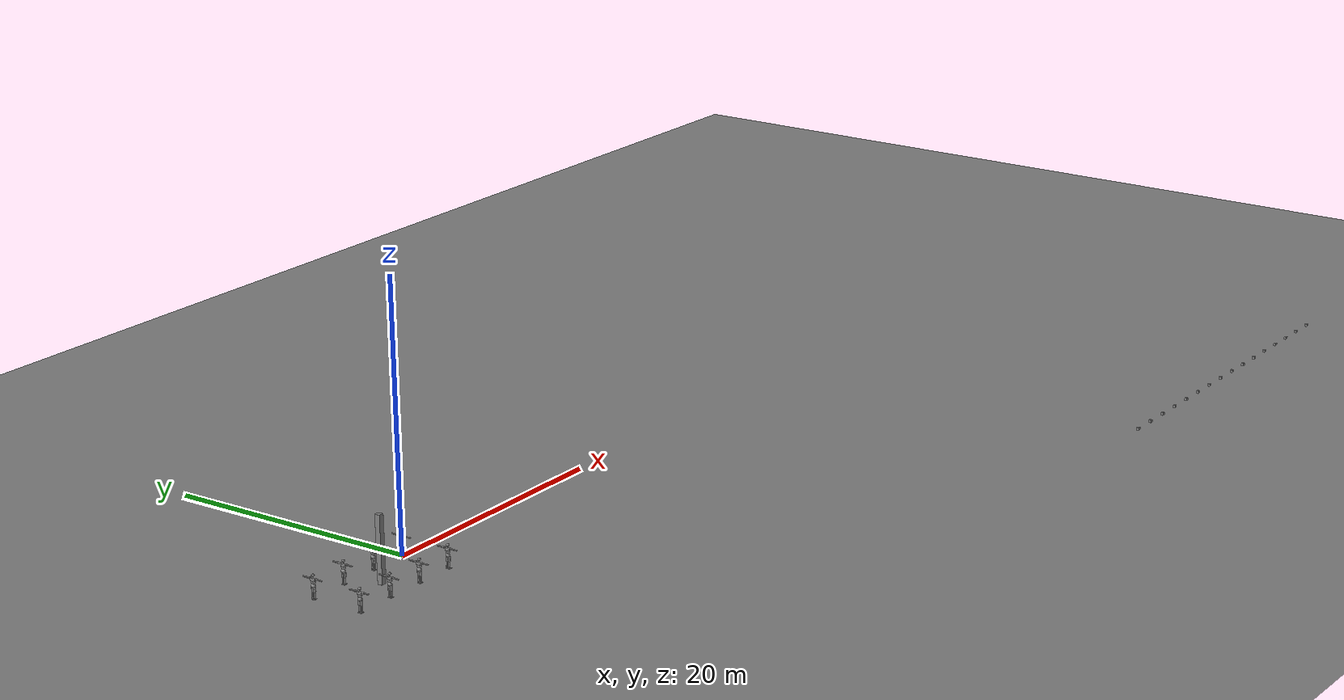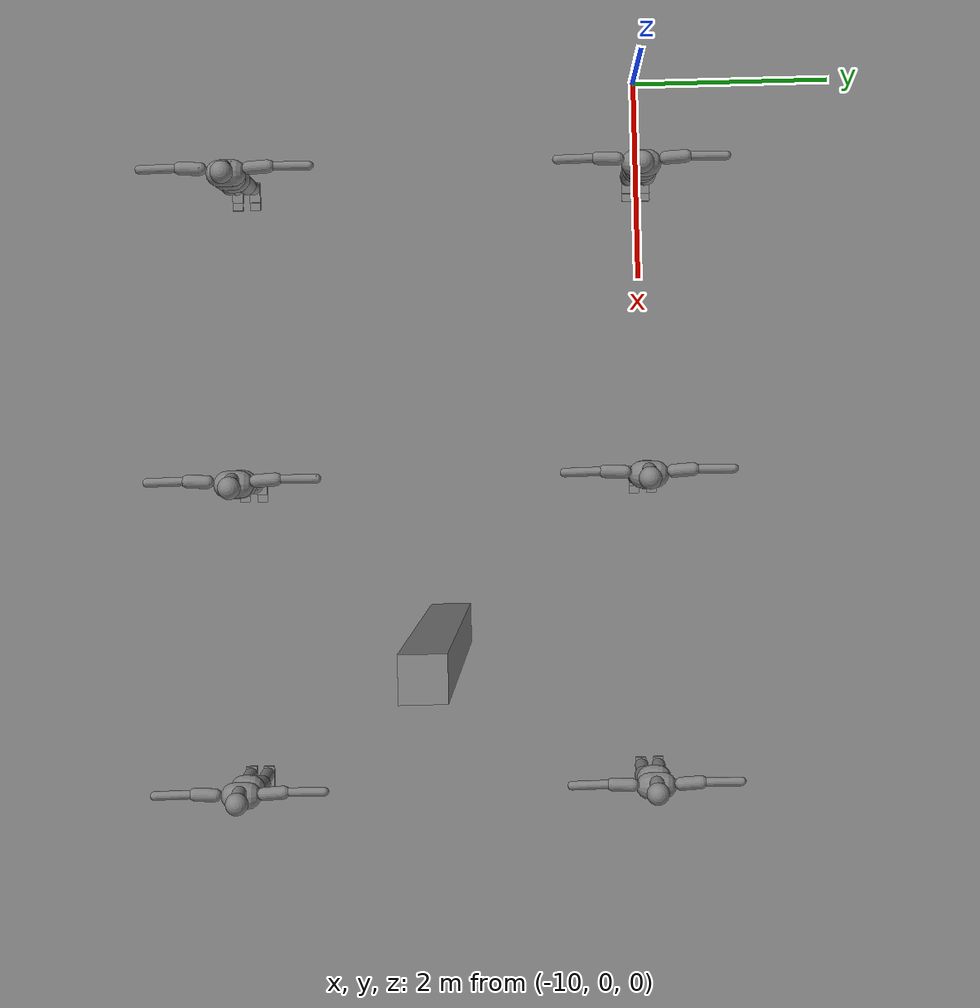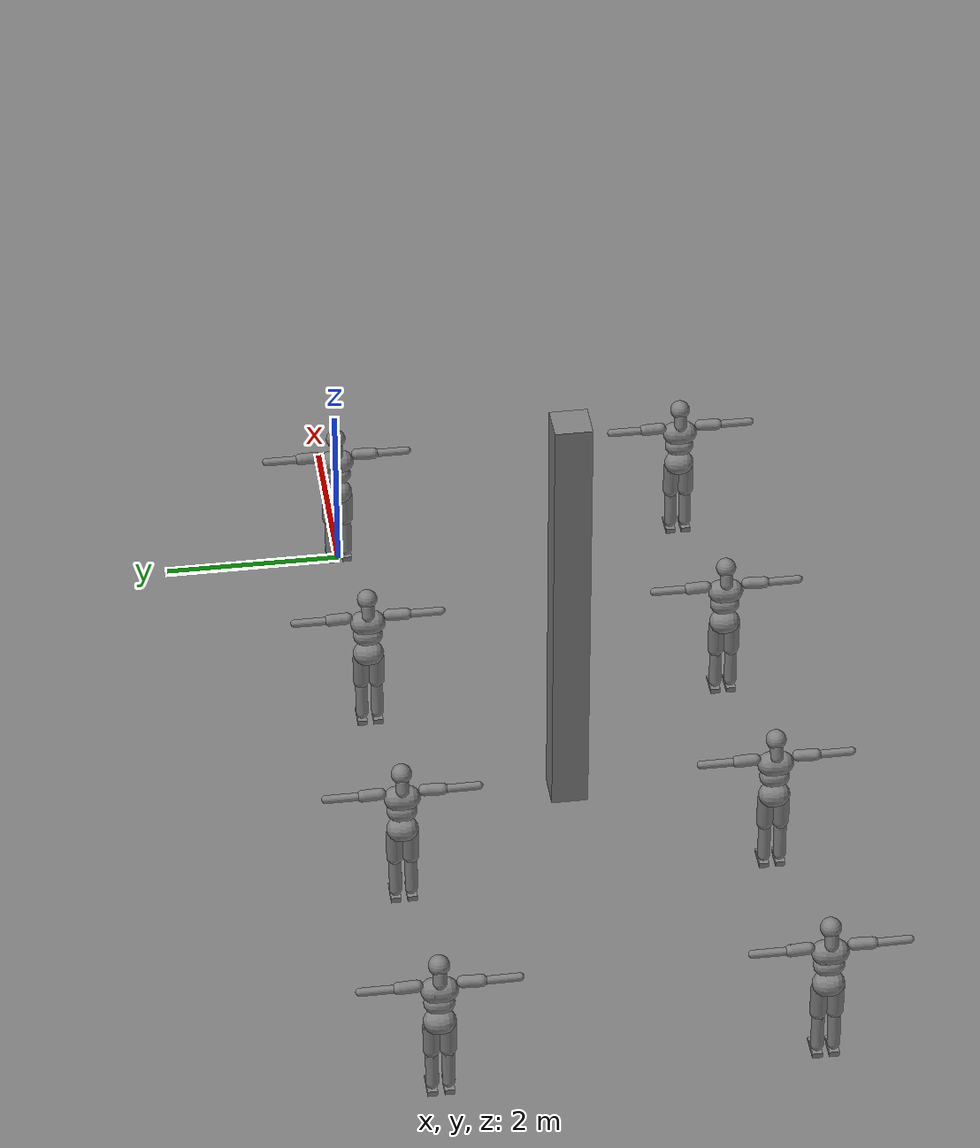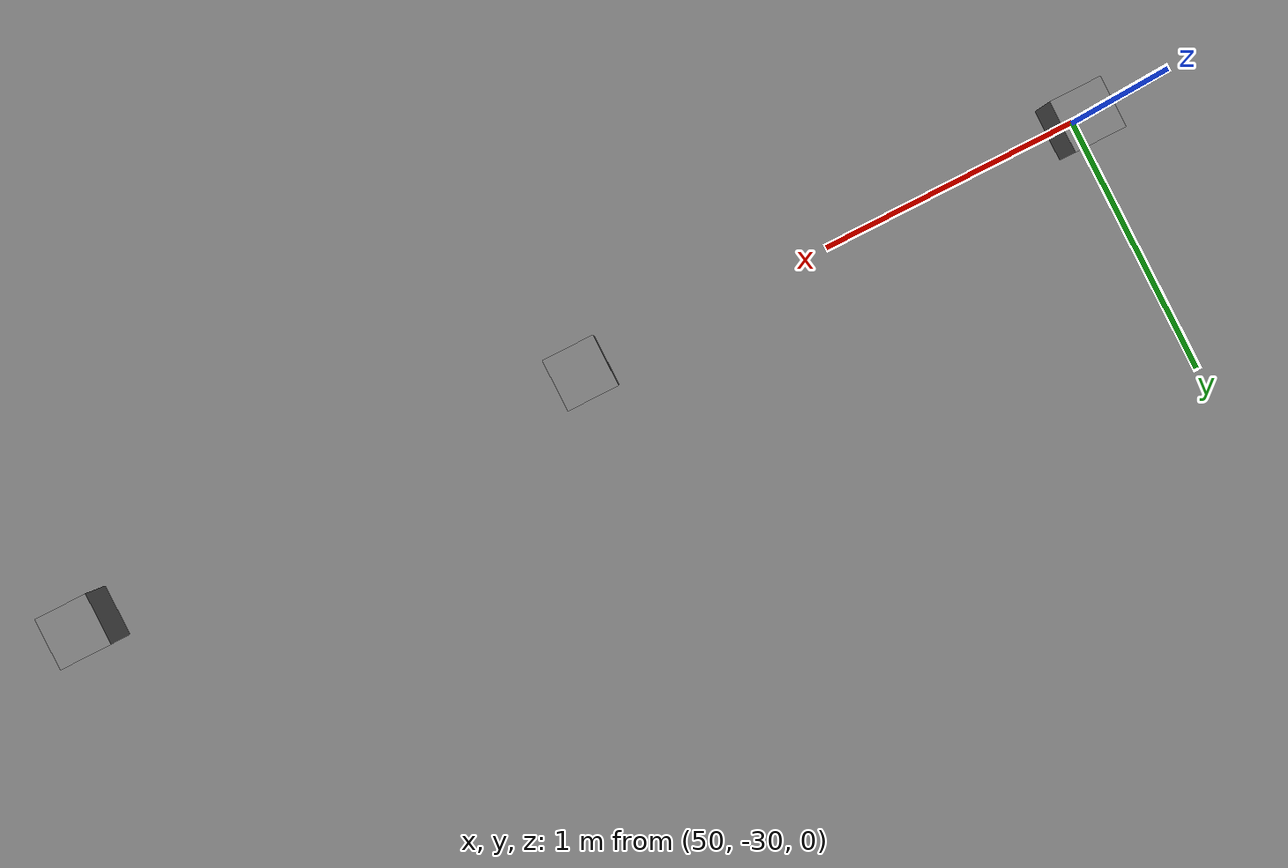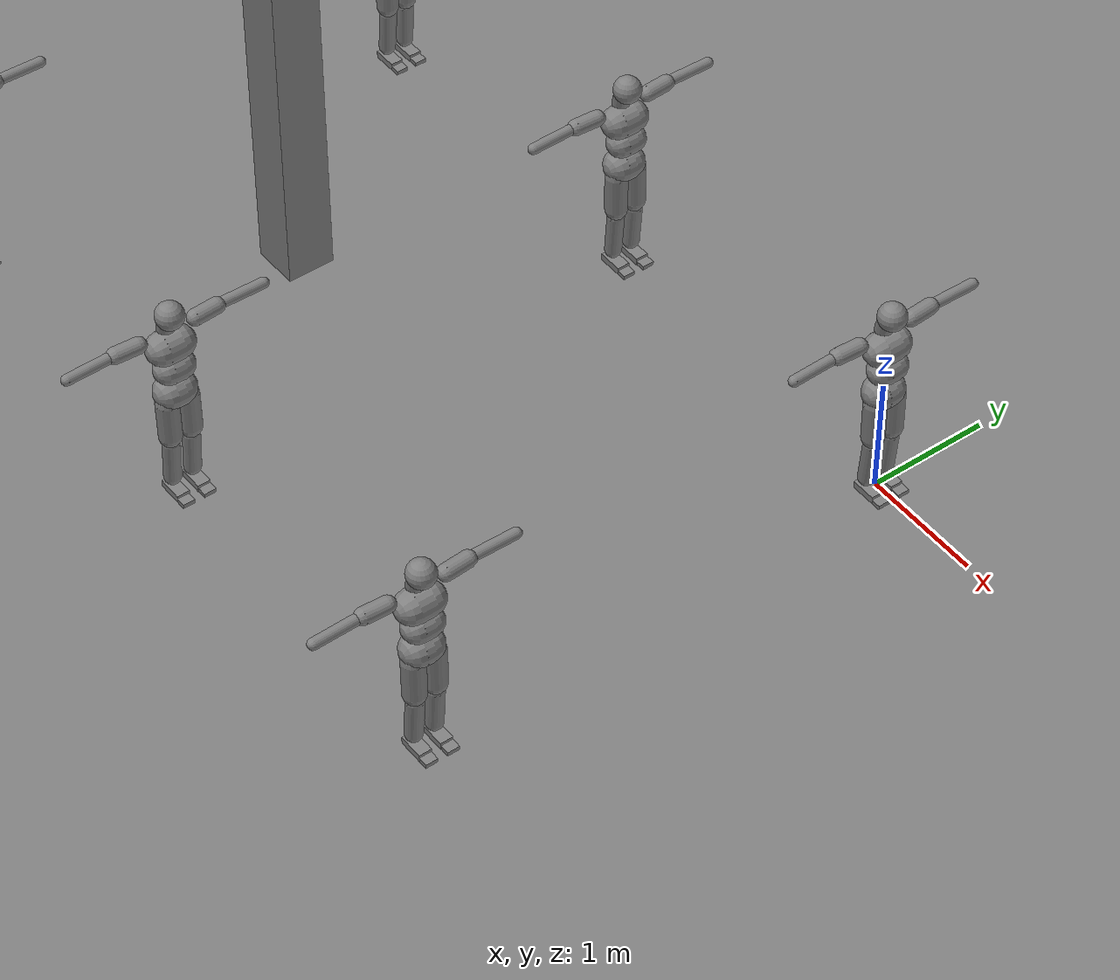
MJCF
<!-- GENERATED by training/tools/compose_mixed.py (march8, lineup mattbio,mattbio,mattbio,mattbio,mattbio,mattbio,mattbio,mattbio). Do not edit. -->
<mujoco model="march8_mixed">
  <compiler angle="degree" autolimits="true" />
  <option timestep="0.005" gravity="0 0 -9.81" integrator="implicitfast" solver="Newton" iterations="20" cone="pyramidal" jacobian="auto">
    <flag multiccd="disable" />
  </option>
  <worldbody>
    <light name="sun" pos="0 0 5" dir="0 0 -1" directional="true" />
    <geom name="ground" type="plane" size="0 0 0.05" contype="65535" conaffinity="65535" condim="3" friction="1 0.005 0.0001" />
    <geom name="metronome" type="box" pos="-4.5 -2 2.5" size="0.2 0.2 2.5" contype="65535" conaffinity="65535" condim="3" friction="1 0.005 0.0001" />
    <body name="L0_pelvis" pos="-8.985941 0 0.966775">
      <inertial pos="-0.01696645 0 -0.003757688" quat="0.7071068 -0.7071068 0 0" mass="8.937766" diaginertia="0.0907144 0.0907144 0.07049761" />
      <freejoint name="L0_root" />
      <geom name="L0_pelvis_geom0" type="capsule" size="0.1357963 0.03473648" contype="65792" conaffinity="16646400" condim="3" friction="1 0.005 0.0001" pos="-0.01696645 0 -0.003757688" quat="0.7071068 -0.7071068 0 0" />
      <body name="L0_torso" pos="-0.000796 0 0.095775">
        <inertial pos="0.003384799 0 0.1412323" quat="0.7071068 -0.7071068 0 0" mass="13.05674" diaginertia="0.1165244 0.1165244 0.08048442" />
        <joint name="L0_abdomen_flex" type="hinge" pos="0 0 0" axis="0 1 0" range="-30 60" armature="0.02" />
        <joint name="L0_abdomen_lat" type="hinge" pos="0 0 0" axis="1 0 0" range="-35 35" armature="0.02" />
        <joint name="L0_abdomen_twist" type="hinge" pos="0 0 0" axis="0 0 1" range="-45 45" armature="0.02" />
        <geom name="L0_torso_geom0" type="capsule" size="0.1189253 0.04429121" contype="65792" conaffinity="16646400" condim="3" friction="1 0.005 0.0001" pos="0.003384799 0 0.1412323" quat="0.7071068 -0.7071068 0 0" />
        <body name="L0_chest" pos="-0.016728 0 0.279754">
          <inertial pos="-0.003824043 0 0.05326067" quat="0.7071068 -0.7071068 0 0" mass="12.76681" diaginertia="0.157376 0.157376 0.09756839" />
          <geom name="L0_chest_geom0" type="capsule" size="0.1315126 0.06314432" contype="65792" conaffinity="16646400" condim="3" friction="1 0.005 0.0001" pos="-0.003824043 0 0.05326067" quat="0.7071068 -0.7071068 0 0" />
          <body name="L0_head" pos="-0.048542 0 0.181344">
            <inertial pos="0.05070428 0 0.1332104" quat="0.6920062 0.1453527 0.1453527 0.6920062" mass="5.548613" diaginertia="0.0503217 0.05005417 0.02171975" />
            <geom name="L0_head_geom0" type="capsule" size="0.06994246 0.0600033" contype="65792" conaffinity="16646400" condim="3" friction="1 0.005 0.0001" pos="0.013404 0 0.058487" quat="0.9936623 0 0.1124062 0" />
            <geom name="L0_head_geom1" type="sphere" size="0.1098854" contype="65792" conaffinity="16646400" condim="3" friction="1 0.005 0.0001" pos="0.07270066 0 0.1772756" />
          </body>
          <body name="L0_upper_arm_l" pos="-0.033514 0.201796 0.161482">
            <inertial pos="-0.007092 0.126 0.00073" quat="0.7091489 -0.7039445 -0.03962202 0" mass="2.169458" diaginertia="0.01610463 0.01610463 0.004156322" />
            <joint name="L0_shoulder_elev_l" type="hinge" pos="0 0 0" axis="1 0 0" range="-95 80" armature="0.01" />
            <joint name="L0_shoulder_flex_l" type="hinge" pos="0 0 0" axis="0 0 -1" range="-60 170" armature="0.01" />
            <joint name="L0_shoulder_twist_l" type="hinge" pos="0 0 0" axis="0 1 0" range="-80 80" armature="0.01" />
            <geom name="L0_upper_arm_l_geom0" type="capsule" size="0.06392297 0.09424006" contype="65792" conaffinity="16646400" condim="3" friction="1 0.005 0.0001" pos="-0.007092 0.126 0.00073" quat="0.7091489 -0.7039445 -0.03962202 0" />
            <body name="L0_forearm_l" pos="-0.014184 0.252 0.00146">
              <inertial pos="0.0027005 0.1902425 -0.00161" quat="0.7041088 -0.7100206 0.01007877 0" mass="1.789553" diaginertia="0.02422419 0.02422419 0.001594476" />
              <joint name="L0_elbow_l" type="hinge" pos="0 0 0" axis="0 0 -1" range="0 145" armature="0.01" />
              <geom name="L0_forearm_l_geom0" type="capsule" size="0.04283781 0.1688496" contype="65792" conaffinity="16646400" condim="3" friction="1 0.005 0.0001" pos="0.0027005 0.1902425 -0.00161" quat="0.7041088 -0.7100206 0.01007877 0" />
            </body>
          </body>
          <body name="L0_upper_arm_r" pos="-0.033514 -0.201796 0.161482">
            <inertial pos="-0.007092 -0.126 0.00073" quat="0.7091489 0.7039445 -0.03962202 0" mass="2.169458" diaginertia="0.01610463 0.01610463 0.004156322" />
            <joint name="L0_shoulder_elev_r" type="hinge" pos="0 0 0" axis="-1 0 0" range="-95 80" armature="0.01" />
            <joint name="L0_shoulder_flex_r" type="hinge" pos="0 0 0" axis="0 0 1" range="-60 170" armature="0.01" />
            <joint name="L0_shoulder_twist_r" type="hinge" pos="0 0 0" axis="0 1 0" range="-80 80" armature="0.01" />
            <geom name="L0_upper_arm_r_geom0" type="capsule" size="0.06392297 0.09424006" contype="65792" conaffinity="16646400" condim="3" friction="1 0.005 0.0001" pos="-0.007092 -0.126 0.00073" quat="0.7091489 0.7039445 -0.03962202 0" />
            <body name="L0_forearm_r" pos="-0.014184 -0.252 0.00146">
              <inertial pos="0.0027005 -0.1902425 -0.00161" quat="0.7041088 0.7100206 0.01007877 0" mass="1.789553" diaginertia="0.02422419 0.02422419 0.001594476" />
              <joint name="L0_elbow_r" type="hinge" pos="0 0 0" axis="0 0 1" range="0 145" armature="0.01" />
              <geom name="L0_forearm_r_geom0" type="capsule" size="0.04283781 0.1688496" contype="65792" conaffinity="16646400" condim="3" friction="1 0.005 0.0001" pos="0.0027005 -0.1902425 -0.00161" quat="0.7041088 0.7100206 0.01007877 0" />
            </body>
          </body>
        </body>
      </body>
      <body name="L0_thigh_l" pos="0.000827 0.085706 -0.03016">
        <inertial pos="0.002864 0 -0.207727" quat="0.006893172 0 0.9999762 0" mass="11.32717" diaginertia="0.2130858 0.2130858 0.04235914" />
        <joint name="L0_hip_flex_l" type="hinge" pos="0 0 0" axis="0 -1 0" range="-30 120" armature="0.02" />
        <joint name="L0_hip_abd_l" type="hinge" pos="0 0 0" axis="1 0 0" range="-30 45" armature="0.02" />
        <joint name="L0_hip_rot_l" type="hinge" pos="0 0 0" axis="0 0 1" range="-40 40" armature="0.02" />
        <geom name="L0_thigh_l_geom0" type="capsule" size="0.08888116 0.1633062" contype="65792" conaffinity="16646400" condim="3" friction="1 0.005 0.0001" pos="0.002864 0 -0.207727" quat="0.006893172 0 0.9999762 0" />
        <body name="L0_shin_l" pos="0.005728 0 -0.415454">
          <inertial pos="-0.0159655 0 -0.214853" quat="0.03707781 0 -0.9993124 0" mass="3.459135" diaginertia="0.06386931 0.06386931 0.007533594" />
          <joint name="L0_knee_l" type="hinge" pos="0 0 0" axis="0 1 0" range="0 150" armature="0.02" />
          <geom name="L0_shin_l_geom0" type="capsule" size="0.06734565 0.1817725" contype="65792" conaffinity="16646400" condim="3" friction="1 0.005 0.0001" pos="-0.0159655 0 -0.214853" quat="0.03707781 0 -0.9993124 0" />
          <body name="L0_foot_l" pos="-0.031931 0 -0.429706">
            <inertial pos="0.03774256 0.002908948 -0.06798844" quat="1 0 0 0" mass="0.8497876" diaginertia="0.00103675 0.003237029 0.003763906" />
            <joint name="L0_ankle_dorsi_l" type="hinge" pos="0 0 0" axis="0 -1 0" range="-50 25" armature="0.01" />
            <joint name="L0_ankle_inv_l" type="hinge" pos="0 0 0" axis="-1 0 0" range="-20 30" armature="0.01" />
            <geom name="L0_foot_l_geom0" type="box" size="0.1026044 0.05253602 0.03" contype="65792" conaffinity="16646400" condim="3" friction="1 0.005 0.0001" pos="0.03774256 0.002908948 -0.06798844" />
            <body name="L0_toe_l" pos="0.140347 0 -0.07597">
              <inertial pos="0.03863281 0.004919875 -0.004518435" quat="1 0 0 0" mass="0.2499375" diaginertia="0.0002352078 0.0001498579 0.0003340368" />
              <joint name="L0_toe_l" type="hinge" pos="0 0 0" axis="0 -1 0" range="-30 60" stiffness="20" damping="1" armature="0.005" />
              <geom name="L0_toe_l_geom0" type="box" size="0.03863281 0.05016921 0.0175" contype="65792" conaffinity="16646400" condim="3" friction="1 0.005 0.0001" pos="0.03863281 0.004919875 -0.004518435" />
            </body>
          </body>
        </body>
      </body>
      <body name="L0_thigh_r" pos="0.000827 -0.085706 -0.03016">
        <inertial pos="0.002864 0 -0.207727" quat="0.006893172 0 0.9999762 0" mass="11.32717" diaginertia="0.2130858 0.2130858 0.04235914" />
        <joint name="L0_hip_flex_r" type="hinge" pos="0 0 0" axis="0 -1 0" range="-30 120" armature="0.02" />
        <joint name="L0_hip_abd_r" type="hinge" pos="0 0 0" axis="-1 0 0" range="-30 45" armature="0.02" />
        <joint name="L0_hip_rot_r" type="hinge" pos="0 0 0" axis="0 0 -1" range="-40 40" armature="0.02" />
        <geom name="L0_thigh_r_geom0" type="capsule" size="0.08888116 0.1633062" contype="65792" conaffinity="16646400" condim="3" friction="1 0.005 0.0001" pos="0.002864 0 -0.207727" quat="0.006893172 0 0.9999762 0" />
        <body name="L0_shin_r" pos="0.005728 0 -0.415454">
          <inertial pos="-0.0159655 0 -0.214853" quat="0.03707781 0 -0.9993124 0" mass="3.459135" diaginertia="0.06386931 0.06386931 0.007533594" />
          <joint name="L0_knee_r" type="hinge" pos="0 0 0" axis="0 1 0" range="0 150" armature="0.02" />
          <geom name="L0_shin_r_geom0" type="capsule" size="0.06734565 0.1817725" contype="65792" conaffinity="16646400" condim="3" friction="1 0.005 0.0001" pos="-0.0159655 0 -0.214853" quat="0.03707781 0 -0.9993124 0" />
          <body name="L0_foot_r" pos="-0.031931 0 -0.429706">
            <inertial pos="0.03774256 -0.002908948 -0.06798844" quat="1 0 0 0" mass="0.8497876" diaginertia="0.00103675 0.003237029 0.003763906" />
            <joint name="L0_ankle_dorsi_r" type="hinge" pos="0 0 0" axis="0 -1 0" range="-50 25" armature="0.01" />
            <joint name="L0_ankle_inv_r" type="hinge" pos="0 0 0" axis="1 0 0" range="-20 30" armature="0.01" />
            <geom name="L0_foot_r_geom0" type="box" size="0.1026044 0.05253602 0.03" contype="65792" conaffinity="16646400" condim="3" friction="1 0.005 0.0001" pos="0.03774256 -0.002908948 -0.06798844" />
            <body name="L0_toe_r" pos="0.140343 0 -0.075843">
              <inertial pos="0.03863281 -0.004919875 -0.004518435" quat="1 0 0 0" mass="0.2499375" diaginertia="0.0002352078 0.0001498579 0.0003340368" />
              <joint name="L0_toe_r" type="hinge" pos="0 0 0" axis="0 -1 0" range="-30 60" stiffness="20" damping="1" armature="0.005" />
              <geom name="L0_toe_r_geom0" type="box" size="0.03863281 0.05016921 0.0175" contype="65792" conaffinity="16646400" condim="3" friction="1 0.005 0.0001" pos="0.03863681 -0.004919875 -0.004645435" />
            </body>
          </body>
        </body>
      </body>
    </body>
    <body name="L1_pelvis" pos="-5.985941 0 0.966775">
      <inertial pos="-0.01696645 0 -0.003757688" quat="0.7071068 -0.7071068 0 0" mass="8.937766" diaginertia="0.0907144 0.0907144 0.07049761" />
      <freejoint name="L1_root" />
      <geom name="L1_pelvis_geom0" type="capsule" size="0.1357963 0.03473648" contype="131584" conaffinity="16581120" condim="3" friction="1 0.005 0.0001" pos="-0.01696645 0 -0.003757688" quat="0.7071068 -0.7071068 0 0" />
      <body name="L1_torso" pos="-0.000796 0 0.095775">
        <inertial pos="0.003384799 0 0.1412323" quat="0.7071068 -0.7071068 0 0" mass="13.05674" diaginertia="0.1165244 0.1165244 0.08048442" />
        <joint name="L1_abdomen_flex" type="hinge" pos="0 0 0" axis="0 1 0" range="-30 60" armature="0.02" />
        <joint name="L1_abdomen_lat" type="hinge" pos="0 0 0" axis="1 0 0" range="-35 35" armature="0.02" />
        <joint name="L1_abdomen_twist" type="hinge" pos="0 0 0" axis="0 0 1" range="-45 45" armature="0.02" />
        <geom name="L1_torso_geom0" type="capsule" size="0.1189253 0.04429121" contype="131584" conaffinity="16581120" condim="3" friction="1 0.005 0.0001" pos="0.003384799 0 0.1412323" quat="0.7071068 -0.7071068 0 0" />
        <body name="L1_chest" pos="-0.016728 0 0.279754">
          <inertial pos="-0.003824043 0 0.05326067" quat="0.7071068 -0.7071068 0 0" mass="12.76681" diaginertia="0.157376 0.157376 0.09756839" />
          <geom name="L1_chest_geom0" type="capsule" size="0.1315126 0.06314432" contype="131584" conaffinity="16581120" condim="3" friction="1 0.005 0.0001" pos="-0.003824043 0 0.05326067" quat="0.7071068 -0.7071068 0 0" />
          <body name="L1_head" pos="-0.048542 0 0.181344">
            <inertial pos="0.05070428 0 0.1332104" quat="0.6920062 0.1453527 0.1453527 0.6920062" mass="5.548613" diaginertia="0.0503217 0.05005417 0.02171975" />
            <geom name="L1_head_geom0" type="capsule" size="0.06994246 0.0600033" contype="131584" conaffinity="16581120" condim="3" friction="1 0.005 0.0001" pos="0.013404 0 0.058487" quat="0.9936623 0 0.1124062 0" />
            <geom name="L1_head_geom1" type="sphere" size="0.1098854" contype="131584" conaffinity="16581120" condim="3" friction="1 0.005 0.0001" pos="0.07270066 0 0.1772756" />
          </body>
          <body name="L1_upper_arm_l" pos="-0.033514 0.201796 0.161482">
            <inertial pos="-0.007092 0.126 0.00073" quat="0.7091489 -0.7039445 -0.03962202 0" mass="2.169458" diaginertia="0.01610463 0.01610463 0.004156322" />
            <joint name="L1_shoulder_elev_l" type="hinge" pos="0 0 0" axis="1 0 0" range="-95 80" armature="0.01" />
            <joint name="L1_shoulder_flex_l" type="hinge" pos="0 0 0" axis="0 0 -1" range="-60 170" armature="0.01" />
            <joint name="L1_shoulder_twist_l" type="hinge" pos="0 0 0" axis="0 1 0" range="-80 80" armature="0.01" />
            <geom name="L1_upper_arm_l_geom0" type="capsule" size="0.06392297 0.09424006" contype="131584" conaffinity="16581120" condim="3" friction="1 0.005 0.0001" pos="-0.007092 0.126 0.00073" quat="0.7091489 -0.7039445 -0.03962202 0" />
            <body name="L1_forearm_l" pos="-0.014184 0.252 0.00146">
              <inertial pos="0.0027005 0.1902425 -0.00161" quat="0.7041088 -0.7100206 0.01007877 0" mass="1.789553" diaginertia="0.02422419 0.02422419 0.001594476" />
              <joint name="L1_elbow_l" type="hinge" pos="0 0 0" axis="0 0 -1" range="0 145" armature="0.01" />
              <geom name="L1_forearm_l_geom0" type="capsule" size="0.04283781 0.1688496" contype="131584" conaffinity="16581120" condim="3" friction="1 0.005 0.0001" pos="0.0027005 0.1902425 -0.00161" quat="0.7041088 -0.7100206 0.01007877 0" />
            </body>
          </body>
          <body name="L1_upper_arm_r" pos="-0.033514 -0.201796 0.161482">
            <inertial pos="-0.007092 -0.126 0.00073" quat="0.7091489 0.7039445 -0.03962202 0" mass="2.169458" diaginertia="0.01610463 0.01610463 0.004156322" />
            <joint name="L1_shoulder_elev_r" type="hinge" pos="0 0 0" axis="-1 0 0" range="-95 80" armature="0.01" />
            <joint name="L1_shoulder_flex_r" type="hinge" pos="0 0 0" axis="0 0 1" range="-60 170" armature="0.01" />
            <joint name="L1_shoulder_twist_r" type="hinge" pos="0 0 0" axis="0 1 0" range="-80 80" armature="0.01" />
            <geom name="L1_upper_arm_r_geom0" type="capsule" size="0.06392297 0.09424006" contype="131584" conaffinity="16581120" condim="3" friction="1 0.005 0.0001" pos="-0.007092 -0.126 0.00073" quat="0.7091489 0.7039445 -0.03962202 0" />
            <body name="L1_forearm_r" pos="-0.014184 -0.252 0.00146">
              <inertial pos="0.0027005 -0.1902425 -0.00161" quat="0.7041088 0.7100206 0.01007877 0" mass="1.789553" diaginertia="0.02422419 0.02422419 0.001594476" />
              <joint name="L1_elbow_r" type="hinge" pos="0 0 0" axis="0 0 1" range="0 145" armature="0.01" />
              <geom name="L1_forearm_r_geom0" type="capsule" size="0.04283781 0.1688496" contype="131584" conaffinity="16581120" condim="3" friction="1 0.005 0.0001" pos="0.0027005 -0.1902425 -0.00161" quat="0.7041088 0.7100206 0.01007877 0" />
            </body>
          </body>
        </body>
      </body>
      <body name="L1_thigh_l" pos="0.000827 0.085706 -0.03016">
        <inertial pos="0.002864 0 -0.207727" quat="0.006893172 0 0.9999762 0" mass="11.32717" diaginertia="0.2130858 0.2130858 0.04235914" />
        <joint name="L1_hip_flex_l" type="hinge" pos="0 0 0" axis="0 -1 0" range="-30 120" armature="0.02" />
        <joint name="L1_hip_abd_l" type="hinge" pos="0 0 0" axis="1 0 0" range="-30 45" armature="0.02" />
        <joint name="L1_hip_rot_l" type="hinge" pos="0 0 0" axis="0 0 1" range="-40 40" armature="0.02" />
        <geom name="L1_thigh_l_geom0" type="capsule" size="0.08888116 0.1633062" contype="131584" conaffinity="16581120" condim="3" friction="1 0.005 0.0001" pos="0.002864 0 -0.207727" quat="0.006893172 0 0.9999762 0" />
        <body name="L1_shin_l" pos="0.005728 0 -0.415454">
          <inertial pos="-0.0159655 0 -0.214853" quat="0.03707781 0 -0.9993124 0" mass="3.459135" diaginertia="0.06386931 0.06386931 0.007533594" />
          <joint name="L1_knee_l" type="hinge" pos="0 0 0" axis="0 1 0" range="0 150" armature="0.02" />
          <geom name="L1_shin_l_geom0" type="capsule" size="0.06734565 0.1817725" contype="131584" conaffinity="16581120" condim="3" friction="1 0.005 0.0001" pos="-0.0159655 0 -0.214853" quat="0.03707781 0 -0.9993124 0" />
          <body name="L1_foot_l" pos="-0.031931 0 -0.429706">
            <inertial pos="0.03774256 0.002908948 -0.06798844" quat="1 0 0 0" mass="0.8497876" diaginertia="0.00103675 0.003237029 0.003763906" />
            <joint name="L1_ankle_dorsi_l" type="hinge" pos="0 0 0" axis="0 -1 0" range="-50 25" armature="0.01" />
            <joint name="L1_ankle_inv_l" type="hinge" pos="0 0 0" axis="-1 0 0" range="-20 30" armature="0.01" />
            <geom name="L1_foot_l_geom0" type="box" size="0.1026044 0.05253602 0.03" contype="131584" conaffinity="16581120" condim="3" friction="1 0.005 0.0001" pos="0.03774256 0.002908948 -0.06798844" />
            <body name="L1_toe_l" pos="0.140347 0 -0.07597">
              <inertial pos="0.03863281 0.004919875 -0.004518435" quat="1 0 0 0" mass="0.2499375" diaginertia="0.0002352078 0.0001498579 0.0003340368" />
              <joint name="L1_toe_l" type="hinge" pos="0 0 0" axis="0 -1 0" range="-30 60" stiffness="20" damping="1" armature="0.005" />
              <geom name="L1_toe_l_geom0" type="box" size="0.03863281 0.05016921 0.0175" contype="131584" conaffinity="16581120" condim="3" friction="1 0.005 0.0001" pos="0.03863281 0.004919875 -0.004518435" />
            </body>
          </body>
        </body>
      </body>
      <body name="L1_thigh_r" pos="0.000827 -0.085706 -0.03016">
        <inertial pos="0.002864 0 -0.207727" quat="0.006893172 0 0.9999762 0" mass="11.32717" diaginertia="0.2130858 0.2130858 0.04235914" />
        <joint name="L1_hip_flex_r" type="hinge" pos="0 0 0" axis="0 -1 0" range="-30 120" armature="0.02" />
        <joint name="L1_hip_abd_r" type="hinge" pos="0 0 0" axis="-1 0 0" range="-30 45" armature="0.02" />
        <joint name="L1_hip_rot_r" type="hinge" pos="0 0 0" axis="0 0 -1" range="-40 40" armature="0.02" />
        <geom name="L1_thigh_r_geom0" type="capsule" size="0.08888116 0.1633062" contype="131584" conaffinity="16581120" condim="3" friction="1 0.005 0.0001" pos="0.002864 0 -0.207727" quat="0.006893172 0 0.9999762 0" />
        <body name="L1_shin_r" pos="0.005728 0 -0.415454">
          <inertial pos="-0.0159655 0 -0.214853" quat="0.03707781 0 -0.9993124 0" mass="3.459135" diaginertia="0.06386931 0.06386931 0.007533594" />
          <joint name="L1_knee_r" type="hinge" pos="0 0 0" axis="0 1 0" range="0 150" armature="0.02" />
          <geom name="L1_shin_r_geom0" type="capsule" size="0.06734565 0.1817725" contype="131584" conaffinity="16581120" condim="3" friction="1 0.005 0.0001" pos="-0.0159655 0 -0.214853" quat="0.03707781 0 -0.9993124 0" />
          <body name="L1_foot_r" pos="-0.031931 0 -0.429706">
            <inertial pos="0.03774256 -0.002908948 -0.06798844" quat="1 0 0 0" mass="0.8497876" diaginertia="0.00103675 0.003237029 0.003763906" />
            <joint name="L1_ankle_dorsi_r" type="hinge" pos="0 0 0" axis="0 -1 0" range="-50 25" armature="0.01" />
            <joint name="L1_ankle_inv_r" type="hinge" pos="0 0 0" axis="1 0 0" range="-20 30" armature="0.01" />
            <geom name="L1_foot_r_geom0" type="box" size="0.1026044 0.05253602 0.03" contype="131584" conaffinity="16581120" condim="3" friction="1 0.005 0.0001" pos="0.03774256 -0.002908948 -0.06798844" />
            <body name="L1_toe_r" pos="0.140343 0 -0.075843">
              <inertial pos="0.03863281 -0.004919875 -0.004518435" quat="1 0 0 0" mass="0.2499375" diaginertia="0.0002352078 0.0001498579 0.0003340368" />
              <joint name="L1_toe_r" type="hinge" pos="0 0 0" axis="0 -1 0" range="-30 60" stiffness="20" damping="1" armature="0.005" />
              <geom name="L1_toe_r_geom0" type="box" size="0.03863281 0.05016921 0.0175" contype="131584" conaffinity="16581120" condim="3" friction="1 0.005 0.0001" pos="0.03863681 -0.004919875 -0.004645435" />
            </body>
          </body>
        </body>
      </body>
    </body>
    <body name="L2_pelvis" pos="-2.985941 0 0.966775">
      <inertial pos="-0.01696645 0 -0.003757688" quat="0.7071068 -0.7071068 0 0" mass="8.937766" diaginertia="0.0907144 0.0907144 0.07049761" />
      <freejoint name="L2_root" />
      <geom name="L2_pelvis_geom0" type="capsule" size="0.1357963 0.03473648" contype="263168" conaffinity="16450560" condim="3" friction="1 0.005 0.0001" pos="-0.01696645 0 -0.003757688" quat="0.7071068 -0.7071068 0 0" />
      <body name="L2_torso" pos="-0.000796 0 0.095775">
        <inertial pos="0.003384799 0 0.1412323" quat="0.7071068 -0.7071068 0 0" mass="13.05674" diaginertia="0.1165244 0.1165244 0.08048442" />
        <joint name="L2_abdomen_flex" type="hinge" pos="0 0 0" axis="0 1 0" range="-30 60" armature="0.02" />
        <joint name="L2_abdomen_lat" type="hinge" pos="0 0 0" axis="1 0 0" range="-35 35" armature="0.02" />
        <joint name="L2_abdomen_twist" type="hinge" pos="0 0 0" axis="0 0 1" range="-45 45" armature="0.02" />
        <geom name="L2_torso_geom0" type="capsule" size="0.1189253 0.04429121" contype="263168" conaffinity="16450560" condim="3" friction="1 0.005 0.0001" pos="0.003384799 0 0.1412323" quat="0.7071068 -0.7071068 0 0" />
        <body name="L2_chest" pos="-0.016728 0 0.279754">
          <inertial pos="-0.003824043 0 0.05326067" quat="0.7071068 -0.7071068 0 0" mass="12.76681" diaginertia="0.157376 0.157376 0.09756839" />
          <geom name="L2_chest_geom0" type="capsule" size="0.1315126 0.06314432" contype="263168" conaffinity="16450560" condim="3" friction="1 0.005 0.0001" pos="-0.003824043 0 0.05326067" quat="0.7071068 -0.7071068 0 0" />
          <body name="L2_head" pos="-0.048542 0 0.181344">
            <inertial pos="0.05070428 0 0.1332104" quat="0.6920062 0.1453527 0.1453527 0.6920062" mass="5.548613" diaginertia="0.0503217 0.05005417 0.02171975" />
            <geom name="L2_head_geom0" type="capsule" size="0.06994246 0.0600033" contype="263168" conaffinity="16450560" condim="3" friction="1 0.005 0.0001" pos="0.013404 0 0.058487" quat="0.9936623 0 0.1124062 0" />
            <geom name="L2_head_geom1" type="sphere" size="0.1098854" contype="263168" conaffinity="16450560" condim="3" friction="1 0.005 0.0001" pos="0.07270066 0 0.1772756" />
          </body>
          <body name="L2_upper_arm_l" pos="-0.033514 0.201796 0.161482">
            <inertial pos="-0.007092 0.126 0.00073" quat="0.7091489 -0.7039445 -0.03962202 0" mass="2.169458" diaginertia="0.01610463 0.01610463 0.004156322" />
            <joint name="L2_shoulder_elev_l" type="hinge" pos="0 0 0" axis="1 0 0" range="-95 80" armature="0.01" />
            <joint name="L2_shoulder_flex_l" type="hinge" pos="0 0 0" axis="0 0 -1" range="-60 170" armature="0.01" />
            <joint name="L2_shoulder_twist_l" type="hinge" pos="0 0 0" axis="0 1 0" range="-80 80" armature="0.01" />
            <geom name="L2_upper_arm_l_geom0" type="capsule" size="0.06392297 0.09424006" contype="263168" conaffinity="16450560" condim="3" friction="1 0.005 0.0001" pos="-0.007092 0.126 0.00073" quat="0.7091489 -0.7039445 -0.03962202 0" />
            <body name="L2_forearm_l" pos="-0.014184 0.252 0.00146">
              <inertial pos="0.0027005 0.1902425 -0.00161" quat="0.7041088 -0.7100206 0.01007877 0" mass="1.789553" diaginertia="0.02422419 0.02422419 0.001594476" />
              <joint name="L2_elbow_l" type="hinge" pos="0 0 0" axis="0 0 -1" range="0 145" armature="0.01" />
              <geom name="L2_forearm_l_geom0" type="capsule" size="0.04283781 0.1688496" contype="263168" conaffinity="16450560" condim="3" friction="1 0.005 0.0001" pos="0.0027005 0.1902425 -0.00161" quat="0.7041088 -0.7100206 0.01007877 0" />
            </body>
          </body>
          <body name="L2_upper_arm_r" pos="-0.033514 -0.201796 0.161482">
            <inertial pos="-0.007092 -0.126 0.00073" quat="0.7091489 0.7039445 -0.03962202 0" mass="2.169458" diaginertia="0.01610463 0.01610463 0.004156322" />
            <joint name="L2_shoulder_elev_r" type="hinge" pos="0 0 0" axis="-1 0 0" range="-95 80" armature="0.01" />
            <joint name="L2_shoulder_flex_r" type="hinge" pos="0 0 0" axis="0 0 1" range="-60 170" armature="0.01" />
            <joint name="L2_shoulder_twist_r" type="hinge" pos="0 0 0" axis="0 1 0" range="-80 80" armature="0.01" />
            <geom name="L2_upper_arm_r_geom0" type="capsule" size="0.06392297 0.09424006" contype="263168" conaffinity="16450560" condim="3" friction="1 0.005 0.0001" pos="-0.007092 -0.126 0.00073" quat="0.7091489 0.7039445 -0.03962202 0" />
            <body name="L2_forearm_r" pos="-0.014184 -0.252 0.00146">
              <inertial pos="0.0027005 -0.1902425 -0.00161" quat="0.7041088 0.7100206 0.01007877 0" mass="1.789553" diaginertia="0.02422419 0.02422419 0.001594476" />
              <joint name="L2_elbow_r" type="hinge" pos="0 0 0" axis="0 0 1" range="0 145" armature="0.01" />
              <geom name="L2_forearm_r_geom0" type="capsule" size="0.04283781 0.1688496" contype="263168" conaffinity="16450560" condim="3" friction="1 0.005 0.0001" pos="0.0027005 -0.1902425 -0.00161" quat="0.7041088 0.7100206 0.01007877 0" />
            </body>
          </body>
        </body>
      </body>
      <body name="L2_thigh_l" pos="0.000827 0.085706 -0.03016">
        <inertial pos="0.002864 0 -0.207727" quat="0.006893172 0 0.9999762 0" mass="11.32717" diaginertia="0.2130858 0.2130858 0.04235914" />
        <joint name="L2_hip_flex_l" type="hinge" pos="0 0 0" axis="0 -1 0" range="-30 120" armature="0.02" />
        <joint name="L2_hip_abd_l" type="hinge" pos="0 0 0" axis="1 0 0" range="-30 45" armature="0.02" />
        <joint name="L2_hip_rot_l" type="hinge" pos="0 0 0" axis="0 0 1" range="-40 40" armature="0.02" />
        <geom name="L2_thigh_l_geom0" type="capsule" size="0.08888116 0.1633062" contype="263168" conaffinity="16450560" condim="3" friction="1 0.005 0.0001" pos="0.002864 0 -0.207727" quat="0.006893172 0 0.9999762 0" />
        <body name="L2_shin_l" pos="0.005728 0 -0.415454">
          <inertial pos="-0.0159655 0 -0.214853" quat="0.03707781 0 -0.9993124 0" mass="3.459135" diaginertia="0.06386931 0.06386931 0.007533594" />
          <joint name="L2_knee_l" type="hinge" pos="0 0 0" axis="0 1 0" range="0 150" armature="0.02" />
          <geom name="L2_shin_l_geom0" type="capsule" size="0.06734565 0.1817725" contype="263168" conaffinity="16450560" condim="3" friction="1 0.005 0.0001" pos="-0.0159655 0 -0.214853" quat="0.03707781 0 -0.9993124 0" />
          <body name="L2_foot_l" pos="-0.031931 0 -0.429706">
            <inertial pos="0.03774256 0.002908948 -0.06798844" quat="1 0 0 0" mass="0.8497876" diaginertia="0.00103675 0.003237029 0.003763906" />
            <joint name="L2_ankle_dorsi_l" type="hinge" pos="0 0 0" axis="0 -1 0" range="-50 25" armature="0.01" />
            <joint name="L2_ankle_inv_l" type="hinge" pos="0 0 0" axis="-1 0 0" range="-20 30" armature="0.01" />
            <geom name="L2_foot_l_geom0" type="box" size="0.1026044 0.05253602 0.03" contype="263168" conaffinity="16450560" condim="3" friction="1 0.005 0.0001" pos="0.03774256 0.002908948 -0.06798844" />
            <body name="L2_toe_l" pos="0.140347 0 -0.07597">
              <inertial pos="0.03863281 0.004919875 -0.004518435" quat="1 0 0 0" mass="0.2499375" diaginertia="0.0002352078 0.0001498579 0.0003340368" />
              <joint name="L2_toe_l" type="hinge" pos="0 0 0" axis="0 -1 0" range="-30 60" stiffness="20" damping="1" armature="0.005" />
              <geom name="L2_toe_l_geom0" type="box" size="0.03863281 0.05016921 0.0175" contype="263168" conaffinity="16450560" condim="3" friction="1 0.005 0.0001" pos="0.03863281 0.004919875 -0.004518435" />
            </body>
          </body>
        </body>
      </body>
      <body name="L2_thigh_r" pos="0.000827 -0.085706 -0.03016">
        <inertial pos="0.002864 0 -0.207727" quat="0.006893172 0 0.9999762 0" mass="11.32717" diaginertia="0.2130858 0.2130858 0.04235914" />
        <joint name="L2_hip_flex_r" type="hinge" pos="0 0 0" axis="0 -1 0" range="-30 120" armature="0.02" />
        <joint name="L2_hip_abd_r" type="hinge" pos="0 0 0" axis="-1 0 0" range="-30 45" armature="0.02" />
        <joint name="L2_hip_rot_r" type="hinge" pos="0 0 0" axis="0 0 -1" range="-40 40" armature="0.02" />
        <geom name="L2_thigh_r_geom0" type="capsule" size="0.08888116 0.1633062" contype="263168" conaffinity="16450560" condim="3" friction="1 0.005 0.0001" pos="0.002864 0 -0.207727" quat="0.006893172 0 0.9999762 0" />
        <body name="L2_shin_r" pos="0.005728 0 -0.415454">
          <inertial pos="-0.0159655 0 -0.214853" quat="0.03707781 0 -0.9993124 0" mass="3.459135" diaginertia="0.06386931 0.06386931 0.007533594" />
          <joint name="L2_knee_r" type="hinge" pos="0 0 0" axis="0 1 0" range="0 150" armature="0.02" />
          <geom name="L2_shin_r_geom0" type="capsule" size="0.06734565 0.1817725" contype="263168" conaffinity="16450560" condim="3" friction="1 0.005 0.0001" pos="-0.0159655 0 -0.214853" quat="0.03707781 0 -0.9993124 0" />
          <body name="L2_foot_r" pos="-0.031931 0 -0.429706">
            <inertial pos="0.03774256 -0.002908948 -0.06798844" quat="1 0 0 0" mass="0.8497876" diaginertia="0.00103675 0.003237029 0.003763906" />
            <joint name="L2_ankle_dorsi_r" type="hinge" pos="0 0 0" axis="0 -1 0" range="-50 25" armature="0.01" />
            <joint name="L2_ankle_inv_r" type="hinge" pos="0 0 0" axis="1 0 0" range="-20 30" armature="0.01" />
            <geom name="L2_foot_r_geom0" type="box" size="0.1026044 0.05253602 0.03" contype="263168" conaffinity="16450560" condim="3" friction="1 0.005 0.0001" pos="0.03774256 -0.002908948 -0.06798844" />
            <body name="L2_toe_r" pos="0.140343 0 -0.075843">
              <inertial pos="0.03863281 -0.004919875 -0.004518435" quat="1 0 0 0" mass="0.2499375" diaginertia="0.0002352078 0.0001498579 0.0003340368" />
              <joint name="L2_toe_r" type="hinge" pos="0 0 0" axis="0 -1 0" range="-30 60" stiffness="20" damping="1" armature="0.005" />
              <geom name="L2_toe_r_geom0" type="box" size="0.03863281 0.05016921 0.0175" contype="263168" conaffinity="16450560" condim="3" friction="1 0.005 0.0001" pos="0.03863681 -0.004919875 -0.004645435" />
            </body>
          </body>
        </body>
      </body>
    </body>
    <body name="L3_pelvis" pos="0.014059 0 0.966775">
      <inertial pos="-0.01696645 0 -0.003757688" quat="0.7071068 -0.7071068 0 0" mass="8.937766" diaginertia="0.0907144 0.0907144 0.07049761" />
      <freejoint name="L3_root" />
      <geom name="L3_pelvis_geom0" type="capsule" size="0.1357963 0.03473648" contype="526336" conaffinity="16189440" condim="3" friction="1 0.005 0.0001" pos="-0.01696645 0 -0.003757688" quat="0.7071068 -0.7071068 0 0" />
      <body name="L3_torso" pos="-0.000796 0 0.095775">
        <inertial pos="0.003384799 0 0.1412323" quat="0.7071068 -0.7071068 0 0" mass="13.05674" diaginertia="0.1165244 0.1165244 0.08048442" />
        <joint name="L3_abdomen_flex" type="hinge" pos="0 0 0" axis="0 1 0" range="-30 60" armature="0.02" />
        <joint name="L3_abdomen_lat" type="hinge" pos="0 0 0" axis="1 0 0" range="-35 35" armature="0.02" />
        <joint name="L3_abdomen_twist" type="hinge" pos="0 0 0" axis="0 0 1" range="-45 45" armature="0.02" />
        <geom name="L3_torso_geom0" type="capsule" size="0.1189253 0.04429121" contype="526336" conaffinity="16189440" condim="3" friction="1 0.005 0.0001" pos="0.003384799 0 0.1412323" quat="0.7071068 -0.7071068 0 0" />
        <body name="L3_chest" pos="-0.016728 0 0.279754">
          <inertial pos="-0.003824043 0 0.05326067" quat="0.7071068 -0.7071068 0 0" mass="12.76681" diaginertia="0.157376 0.157376 0.09756839" />
          <geom name="L3_chest_geom0" type="capsule" size="0.1315126 0.06314432" contype="526336" conaffinity="16189440" condim="3" friction="1 0.005 0.0001" pos="-0.003824043 0 0.05326067" quat="0.7071068 -0.7071068 0 0" />
          <body name="L3_head" pos="-0.048542 0 0.181344">
            <inertial pos="0.05070428 0 0.1332104" quat="0.6920062 0.1453527 0.1453527 0.6920062" mass="5.548613" diaginertia="0.0503217 0.05005417 0.02171975" />
            <geom name="L3_head_geom0" type="capsule" size="0.06994246 0.0600033" contype="526336" conaffinity="16189440" condim="3" friction="1 0.005 0.0001" pos="0.013404 0 0.058487" quat="0.9936623 0 0.1124062 0" />
            <geom name="L3_head_geom1" type="sphere" size="0.1098854" contype="526336" conaffinity="16189440" condim="3" friction="1 0.005 0.0001" pos="0.07270066 0 0.1772756" />
          </body>
          <body name="L3_upper_arm_l" pos="-0.033514 0.201796 0.161482">
            <inertial pos="-0.007092 0.126 0.00073" quat="0.7091489 -0.7039445 -0.03962202 0" mass="2.169458" diaginertia="0.01610463 0.01610463 0.004156322" />
            <joint name="L3_shoulder_elev_l" type="hinge" pos="0 0 0" axis="1 0 0" range="-95 80" armature="0.01" />
            <joint name="L3_shoulder_flex_l" type="hinge" pos="0 0 0" axis="0 0 -1" range="-60 170" armature="0.01" />
            <joint name="L3_shoulder_twist_l" type="hinge" pos="0 0 0" axis="0 1 0" range="-80 80" armature="0.01" />
            <geom name="L3_upper_arm_l_geom0" type="capsule" size="0.06392297 0.09424006" contype="526336" conaffinity="16189440" condim="3" friction="1 0.005 0.0001" pos="-0.007092 0.126 0.00073" quat="0.7091489 -0.7039445 -0.03962202 0" />
            <body name="L3_forearm_l" pos="-0.014184 0.252 0.00146">
              <inertial pos="0.0027005 0.1902425 -0.00161" quat="0.7041088 -0.7100206 0.01007877 0" mass="1.789553" diaginertia="0.02422419 0.02422419 0.001594476" />
              <joint name="L3_elbow_l" type="hinge" pos="0 0 0" axis="0 0 -1" range="0 145" armature="0.01" />
              <geom name="L3_forearm_l_geom0" type="capsule" size="0.04283781 0.1688496" contype="526336" conaffinity="16189440" condim="3" friction="1 0.005 0.0001" pos="0.0027005 0.1902425 -0.00161" quat="0.7041088 -0.7100206 0.01007877 0" />
            </body>
          </body>
          <body name="L3_upper_arm_r" pos="-0.033514 -0.201796 0.161482">
            <inertial pos="-0.007092 -0.126 0.00073" quat="0.7091489 0.7039445 -0.03962202 0" mass="2.169458" diaginertia="0.01610463 0.01610463 0.004156322" />
            <joint name="L3_shoulder_elev_r" type="hinge" pos="0 0 0" axis="-1 0 0" range="-95 80" armature="0.01" />
            <joint name="L3_shoulder_flex_r" type="hinge" pos="0 0 0" axis="0 0 1" range="-60 170" armature="0.01" />
            <joint name="L3_shoulder_twist_r" type="hinge" pos="0 0 0" axis="0 1 0" range="-80 80" armature="0.01" />
            <geom name="L3_upper_arm_r_geom0" type="capsule" size="0.06392297 0.09424006" contype="526336" conaffinity="16189440" condim="3" friction="1 0.005 0.0001" pos="-0.007092 -0.126 0.00073" quat="0.7091489 0.7039445 -0.03962202 0" />
            <body name="L3_forearm_r" pos="-0.014184 -0.252 0.00146">
              <inertial pos="0.0027005 -0.1902425 -0.00161" quat="0.7041088 0.7100206 0.01007877 0" mass="1.789553" diaginertia="0.02422419 0.02422419 0.001594476" />
              <joint name="L3_elbow_r" type="hinge" pos="0 0 0" axis="0 0 1" range="0 145" armature="0.01" />
              <geom name="L3_forearm_r_geom0" type="capsule" size="0.04283781 0.1688496" contype="526336" conaffinity="16189440" condim="3" friction="1 0.005 0.0001" pos="0.0027005 -0.1902425 -0.00161" quat="0.7041088 0.7100206 0.01007877 0" />
            </body>
          </body>
        </body>
      </body>
      <body name="L3_thigh_l" pos="0.000827 0.085706 -0.03016">
        <inertial pos="0.002864 0 -0.207727" quat="0.006893172 0 0.9999762 0" mass="11.32717" diaginertia="0.2130858 0.2130858 0.04235914" />
        <joint name="L3_hip_flex_l" type="hinge" pos="0 0 0" axis="0 -1 0" range="-30 120" armature="0.02" />
        <joint name="L3_hip_abd_l" type="hinge" pos="0 0 0" axis="1 0 0" range="-30 45" armature="0.02" />
        <joint name="L3_hip_rot_l" type="hinge" pos="0 0 0" axis="0 0 1" range="-40 40" armature="0.02" />
        <geom name="L3_thigh_l_geom0" type="capsule" size="0.08888116 0.1633062" contype="526336" conaffinity="16189440" condim="3" friction="1 0.005 0.0001" pos="0.002864 0 -0.207727" quat="0.006893172 0 0.9999762 0" />
        <body name="L3_shin_l" pos="0.005728 0 -0.415454">
          <inertial pos="-0.0159655 0 -0.214853" quat="0.03707781 0 -0.9993124 0" mass="3.459135" diaginertia="0.06386931 0.06386931 0.007533594" />
          <joint name="L3_knee_l" type="hinge" pos="0 0 0" axis="0 1 0" range="0 150" armature="0.02" />
          <geom name="L3_shin_l_geom0" type="capsule" size="0.06734565 0.1817725" contype="526336" conaffinity="16189440" condim="3" friction="1 0.005 0.0001" pos="-0.0159655 0 -0.214853" quat="0.03707781 0 -0.9993124 0" />
          <body name="L3_foot_l" pos="-0.031931 0 -0.429706">
            <inertial pos="0.03774256 0.002908948 -0.06798844" quat="1 0 0 0" mass="0.8497876" diaginertia="0.00103675 0.003237029 0.003763906" />
            <joint name="L3_ankle_dorsi_l" type="hinge" pos="0 0 0" axis="0 -1 0" range="-50 25" armature="0.01" />
            <joint name="L3_ankle_inv_l" type="hinge" pos="0 0 0" axis="-1 0 0" range="-20 30" armature="0.01" />
            <geom name="L3_foot_l_geom0" type="box" size="0.1026044 0.05253602 0.03" contype="526336" conaffinity="16189440" condim="3" friction="1 0.005 0.0001" pos="0.03774256 0.002908948 -0.06798844" />
            <body name="L3_toe_l" pos="0.140347 0 -0.07597">
              <inertial pos="0.03863281 0.004919875 -0.004518435" quat="1 0 0 0" mass="0.2499375" diaginertia="0.0002352078 0.0001498579 0.0003340368" />
              <joint name="L3_toe_l" type="hinge" pos="0 0 0" axis="0 -1 0" range="-30 60" stiffness="20" damping="1" armature="0.005" />
              <geom name="L3_toe_l_geom0" type="box" size="0.03863281 0.05016921 0.0175" contype="526336" conaffinity="16189440" condim="3" friction="1 0.005 0.0001" pos="0.03863281 0.004919875 -0.004518435" />
            </body>
          </body>
        </body>
      </body>
      <body name="L3_thigh_r" pos="0.000827 -0.085706 -0.03016">
        <inertial pos="0.002864 0 -0.207727" quat="0.006893172 0 0.9999762 0" mass="11.32717" diaginertia="0.2130858 0.2130858 0.04235914" />
        <joint name="L3_hip_flex_r" type="hinge" pos="0 0 0" axis="0 -1 0" range="-30 120" armature="0.02" />
        <joint name="L3_hip_abd_r" type="hinge" pos="0 0 0" axis="-1 0 0" range="-30 45" armature="0.02" />
        <joint name="L3_hip_rot_r" type="hinge" pos="0 0 0" axis="0 0 -1" range="-40 40" armature="0.02" />
        <geom name="L3_thigh_r_geom0" type="capsule" size="0.08888116 0.1633062" contype="526336" conaffinity="16189440" condim="3" friction="1 0.005 0.0001" pos="0.002864 0 -0.207727" quat="0.006893172 0 0.9999762 0" />
        <body name="L3_shin_r" pos="0.005728 0 -0.415454">
          <inertial pos="-0.0159655 0 -0.214853" quat="0.03707781 0 -0.9993124 0" mass="3.459135" diaginertia="0.06386931 0.06386931 0.007533594" />
          <joint name="L3_knee_r" type="hinge" pos="0 0 0" axis="0 1 0" range="0 150" armature="0.02" />
          <geom name="L3_shin_r_geom0" type="capsule" size="0.06734565 0.1817725" contype="526336" conaffinity="16189440" condim="3" friction="1 0.005 0.0001" pos="-0.0159655 0 -0.214853" quat="0.03707781 0 -0.9993124 0" />
          <body name="L3_foot_r" pos="-0.031931 0 -0.429706">
            <inertial pos="0.03774256 -0.002908948 -0.06798844" quat="1 0 0 0" mass="0.8497876" diaginertia="0.00103675 0.003237029 0.003763906" />
            <joint name="L3_ankle_dorsi_r" type="hinge" pos="0 0 0" axis="0 -1 0" range="-50 25" armature="0.01" />
            <joint name="L3_ankle_inv_r" type="hinge" pos="0 0 0" axis="1 0 0" range="-20 30" armature="0.01" />
            <geom name="L3_foot_r_geom0" type="box" size="0.1026044 0.05253602 0.03" contype="526336" conaffinity="16189440" condim="3" friction="1 0.005 0.0001" pos="0.03774256 -0.002908948 -0.06798844" />
            <body name="L3_toe_r" pos="0.140343 0 -0.075843">
              <inertial pos="0.03863281 -0.004919875 -0.004518435" quat="1 0 0 0" mass="0.2499375" diaginertia="0.0002352078 0.0001498579 0.0003340368" />
              <joint name="L3_toe_r" type="hinge" pos="0 0 0" axis="0 -1 0" range="-30 60" stiffness="20" damping="1" armature="0.005" />
              <geom name="L3_toe_r_geom0" type="box" size="0.03863281 0.05016921 0.0175" contype="526336" conaffinity="16189440" condim="3" friction="1 0.005 0.0001" pos="0.03863681 -0.004919875 -0.004645435" />
            </body>
          </body>
        </body>
      </body>
    </body>
    <body name="L4_pelvis" pos="-8.985941 -4 0.966775">
      <inertial pos="-0.01696645 0 -0.003757688" quat="0.7071068 -0.7071068 0 0" mass="8.937766" diaginertia="0.0907144 0.0907144 0.07049761" />
      <freejoint name="L4_root" />
      <geom name="L4_pelvis_geom0" type="capsule" size="0.1357963 0.03473648" contype="1052672" conaffinity="15667200" condim="3" friction="1 0.005 0.0001" pos="-0.01696645 0 -0.003757688" quat="0.7071068 -0.7071068 0 0" />
      <body name="L4_torso" pos="-0.000796 0 0.095775">
        <inertial pos="0.003384799 0 0.1412323" quat="0.7071068 -0.7071068 0 0" mass="13.05674" diaginertia="0.1165244 0.1165244 0.08048442" />
        <joint name="L4_abdomen_flex" type="hinge" pos="0 0 0" axis="0 1 0" range="-30 60" armature="0.02" />
        <joint name="L4_abdomen_lat" type="hinge" pos="0 0 0" axis="1 0 0" range="-35 35" armature="0.02" />
        <joint name="L4_abdomen_twist" type="hinge" pos="0 0 0" axis="0 0 1" range="-45 45" armature="0.02" />
        <geom name="L4_torso_geom0" type="capsule" size="0.1189253 0.04429121" contype="1052672" conaffinity="15667200" condim="3" friction="1 0.005 0.0001" pos="0.003384799 0 0.1412323" quat="0.7071068 -0.7071068 0 0" />
        <body name="L4_chest" pos="-0.016728 0 0.279754">
          <inertial pos="-0.003824043 0 0.05326067" quat="0.7071068 -0.7071068 0 0" mass="12.76681" diaginertia="0.157376 0.157376 0.09756839" />
          <geom name="L4_chest_geom0" type="capsule" size="0.1315126 0.06314432" contype="1052672" conaffinity="15667200" condim="3" friction="1 0.005 0.0001" pos="-0.003824043 0 0.05326067" quat="0.7071068 -0.7071068 0 0" />
          <body name="L4_head" pos="-0.048542 0 0.181344">
            <inertial pos="0.05070428 0 0.1332104" quat="0.6920062 0.1453527 0.1453527 0.6920062" mass="5.548613" diaginertia="0.0503217 0.05005417 0.02171975" />
            <geom name="L4_head_geom0" type="capsule" size="0.06994246 0.0600033" contype="1052672" conaffinity="15667200" condim="3" friction="1 0.005 0.0001" pos="0.013404 0 0.058487" quat="0.9936623 0 0.1124062 0" />
            <geom name="L4_head_geom1" type="sphere" size="0.1098854" contype="1052672" conaffinity="15667200" condim="3" friction="1 0.005 0.0001" pos="0.07270066 0 0.1772756" />
          </body>
          <body name="L4_upper_arm_l" pos="-0.033514 0.201796 0.161482">
            <inertial pos="-0.007092 0.126 0.00073" quat="0.7091489 -0.7039445 -0.03962202 0" mass="2.169458" diaginertia="0.01610463 0.01610463 0.004156322" />
            <joint name="L4_shoulder_elev_l" type="hinge" pos="0 0 0" axis="1 0 0" range="-95 80" armature="0.01" />
            <joint name="L4_shoulder_flex_l" type="hinge" pos="0 0 0" axis="0 0 -1" range="-60 170" armature="0.01" />
            <joint name="L4_shoulder_twist_l" type="hinge" pos="0 0 0" axis="0 1 0" range="-80 80" armature="0.01" />
            <geom name="L4_upper_arm_l_geom0" type="capsule" size="0.06392297 0.09424006" contype="1052672" conaffinity="15667200" condim="3" friction="1 0.005 0.0001" pos="-0.007092 0.126 0.00073" quat="0.7091489 -0.7039445 -0.03962202 0" />
            <body name="L4_forearm_l" pos="-0.014184 0.252 0.00146">
              <inertial pos="0.0027005 0.1902425 -0.00161" quat="0.7041088 -0.7100206 0.01007877 0" mass="1.789553" diaginertia="0.02422419 0.02422419 0.001594476" />
              <joint name="L4_elbow_l" type="hinge" pos="0 0 0" axis="0 0 -1" range="0 145" armature="0.01" />
              <geom name="L4_forearm_l_geom0" type="capsule" size="0.04283781 0.1688496" contype="1052672" conaffinity="15667200" condim="3" friction="1 0.005 0.0001" pos="0.0027005 0.1902425 -0.00161" quat="0.7041088 -0.7100206 0.01007877 0" />
            </body>
          </body>
          <body name="L4_upper_arm_r" pos="-0.033514 -0.201796 0.161482">
            <inertial pos="-0.007092 -0.126 0.00073" quat="0.7091489 0.7039445 -0.03962202 0" mass="2.169458" diaginertia="0.01610463 0.01610463 0.004156322" />
            <joint name="L4_shoulder_elev_r" type="hinge" pos="0 0 0" axis="-1 0 0" range="-95 80" armature="0.01" />
            <joint name="L4_shoulder_flex_r" type="hinge" pos="0 0 0" axis="0 0 1" range="-60 170" armature="0.01" />
            <joint name="L4_shoulder_twist_r" type="hinge" pos="0 0 0" axis="0 1 0" range="-80 80" armature="0.01" />
            <geom name="L4_upper_arm_r_geom0" type="capsule" size="0.06392297 0.09424006" contype="1052672" conaffinity="15667200" condim="3" friction="1 0.005 0.0001" pos="-0.007092 -0.126 0.00073" quat="0.7091489 0.7039445 -0.03962202 0" />
            <body name="L4_forearm_r" pos="-0.014184 -0.252 0.00146">
              <inertial pos="0.0027005 -0.1902425 -0.00161" quat="0.7041088 0.7100206 0.01007877 0" mass="1.789553" diaginertia="0.02422419 0.02422419 0.001594476" />
              <joint name="L4_elbow_r" type="hinge" pos="0 0 0" axis="0 0 1" range="0 145" armature="0.01" />
              <geom name="L4_forearm_r_geom0" type="capsule" size="0.04283781 0.1688496" contype="1052672" conaffinity="15667200" condim="3" friction="1 0.005 0.0001" pos="0.0027005 -0.1902425 -0.00161" quat="0.7041088 0.7100206 0.01007877 0" />
            </body>
          </body>
        </body>
      </body>
      <body name="L4_thigh_l" pos="0.000827 0.085706 -0.03016">
        <inertial pos="0.002864 0 -0.207727" quat="0.006893172 0 0.9999762 0" mass="11.32717" diaginertia="0.2130858 0.2130858 0.04235914" />
        <joint name="L4_hip_flex_l" type="hinge" pos="0 0 0" axis="0 -1 0" range="-30 120" armature="0.02" />
        <joint name="L4_hip_abd_l" type="hinge" pos="0 0 0" axis="1 0 0" range="-30 45" armature="0.02" />
        <joint name="L4_hip_rot_l" type="hinge" pos="0 0 0" axis="0 0 1" range="-40 40" armature="0.02" />
        <geom name="L4_thigh_l_geom0" type="capsule" size="0.08888116 0.1633062" contype="1052672" conaffinity="15667200" condim="3" friction="1 0.005 0.0001" pos="0.002864 0 -0.207727" quat="0.006893172 0 0.9999762 0" />
        <body name="L4_shin_l" pos="0.005728 0 -0.415454">
          <inertial pos="-0.0159655 0 -0.214853" quat="0.03707781 0 -0.9993124 0" mass="3.459135" diaginertia="0.06386931 0.06386931 0.007533594" />
          <joint name="L4_knee_l" type="hinge" pos="0 0 0" axis="0 1 0" range="0 150" armature="0.02" />
          <geom name="L4_shin_l_geom0" type="capsule" size="0.06734565 0.1817725" contype="1052672" conaffinity="15667200" condim="3" friction="1 0.005 0.0001" pos="-0.0159655 0 -0.214853" quat="0.03707781 0 -0.9993124 0" />
          <body name="L4_foot_l" pos="-0.031931 0 -0.429706">
            <inertial pos="0.03774256 0.002908948 -0.06798844" quat="1 0 0 0" mass="0.8497876" diaginertia="0.00103675 0.003237029 0.003763906" />
            <joint name="L4_ankle_dorsi_l" type="hinge" pos="0 0 0" axis="0 -1 0" range="-50 25" armature="0.01" />
            <joint name="L4_ankle_inv_l" type="hinge" pos="0 0 0" axis="-1 0 0" range="-20 30" armature="0.01" />
            <geom name="L4_foot_l_geom0" type="box" size="0.1026044 0.05253602 0.03" contype="1052672" conaffinity="15667200" condim="3" friction="1 0.005 0.0001" pos="0.03774256 0.002908948 -0.06798844" />
            <body name="L4_toe_l" pos="0.140347 0 -0.07597">
              <inertial pos="0.03863281 0.004919875 -0.004518435" quat="1 0 0 0" mass="0.2499375" diaginertia="0.0002352078 0.0001498579 0.0003340368" />
              <joint name="L4_toe_l" type="hinge" pos="0 0 0" axis="0 -1 0" range="-30 60" stiffness="20" damping="1" armature="0.005" />
              <geom name="L4_toe_l_geom0" type="box" size="0.03863281 0.05016921 0.0175" contype="1052672" conaffinity="15667200" condim="3" friction="1 0.005 0.0001" pos="0.03863281 0.004919875 -0.004518435" />
            </body>
          </body>
        </body>
      </body>
      <body name="L4_thigh_r" pos="0.000827 -0.085706 -0.03016">
        <inertial pos="0.002864 0 -0.207727" quat="0.006893172 0 0.9999762 0" mass="11.32717" diaginertia="0.2130858 0.2130858 0.04235914" />
        <joint name="L4_hip_flex_r" type="hinge" pos="0 0 0" axis="0 -1 0" range="-30 120" armature="0.02" />
        <joint name="L4_hip_abd_r" type="hinge" pos="0 0 0" axis="-1 0 0" range="-30 45" armature="0.02" />
        <joint name="L4_hip_rot_r" type="hinge" pos="0 0 0" axis="0 0 -1" range="-40 40" armature="0.02" />
        <geom name="L4_thigh_r_geom0" type="capsule" size="0.08888116 0.1633062" contype="1052672" conaffinity="15667200" condim="3" friction="1 0.005 0.0001" pos="0.002864 0 -0.207727" quat="0.006893172 0 0.9999762 0" />
        <body name="L4_shin_r" pos="0.005728 0 -0.415454">
          <inertial pos="-0.0159655 0 -0.214853" quat="0.03707781 0 -0.9993124 0" mass="3.459135" diaginertia="0.06386931 0.06386931 0.007533594" />
          <joint name="L4_knee_r" type="hinge" pos="0 0 0" axis="0 1 0" range="0 150" armature="0.02" />
          <geom name="L4_shin_r_geom0" type="capsule" size="0.06734565 0.1817725" contype="1052672" conaffinity="15667200" condim="3" friction="1 0.005 0.0001" pos="-0.0159655 0 -0.214853" quat="0.03707781 0 -0.9993124 0" />
          <body name="L4_foot_r" pos="-0.031931 0 -0.429706">
            <inertial pos="0.03774256 -0.002908948 -0.06798844" quat="1 0 0 0" mass="0.8497876" diaginertia="0.00103675 0.003237029 0.003763906" />
            <joint name="L4_ankle_dorsi_r" type="hinge" pos="0 0 0" axis="0 -1 0" range="-50 25" armature="0.01" />
            <joint name="L4_ankle_inv_r" type="hinge" pos="0 0 0" axis="1 0 0" range="-20 30" armature="0.01" />
            <geom name="L4_foot_r_geom0" type="box" size="0.1026044 0.05253602 0.03" contype="1052672" conaffinity="15667200" condim="3" friction="1 0.005 0.0001" pos="0.03774256 -0.002908948 -0.06798844" />
            <body name="L4_toe_r" pos="0.140343 0 -0.075843">
              <inertial pos="0.03863281 -0.004919875 -0.004518435" quat="1 0 0 0" mass="0.2499375" diaginertia="0.0002352078 0.0001498579 0.0003340368" />
              <joint name="L4_toe_r" type="hinge" pos="0 0 0" axis="0 -1 0" range="-30 60" stiffness="20" damping="1" armature="0.005" />
              <geom name="L4_toe_r_geom0" type="box" size="0.03863281 0.05016921 0.0175" contype="1052672" conaffinity="15667200" condim="3" friction="1 0.005 0.0001" pos="0.03863681 -0.004919875 -0.004645435" />
            </body>
          </body>
        </body>
      </body>
    </body>
    <body name="L5_pelvis" pos="-5.985941 -4 0.966775">
      <inertial pos="-0.01696645 0 -0.003757688" quat="0.7071068 -0.7071068 0 0" mass="8.937766" diaginertia="0.0907144 0.0907144 0.07049761" />
      <freejoint name="L5_root" />
      <geom name="L5_pelvis_geom0" type="capsule" size="0.1357963 0.03473648" contype="2105344" conaffinity="14622720" condim="3" friction="1 0.005 0.0001" pos="-0.01696645 0 -0.003757688" quat="0.7071068 -0.7071068 0 0" />
      <body name="L5_torso" pos="-0.000796 0 0.095775">
        <inertial pos="0.003384799 0 0.1412323" quat="0.7071068 -0.7071068 0 0" mass="13.05674" diaginertia="0.1165244 0.1165244 0.08048442" />
        <joint name="L5_abdomen_flex" type="hinge" pos="0 0 0" axis="0 1 0" range="-30 60" armature="0.02" />
        <joint name="L5_abdomen_lat" type="hinge" pos="0 0 0" axis="1 0 0" range="-35 35" armature="0.02" />
        <joint name="L5_abdomen_twist" type="hinge" pos="0 0 0" axis="0 0 1" range="-45 45" armature="0.02" />
        <geom name="L5_torso_geom0" type="capsule" size="0.1189253 0.04429121" contype="2105344" conaffinity="14622720" condim="3" friction="1 0.005 0.0001" pos="0.003384799 0 0.1412323" quat="0.7071068 -0.7071068 0 0" />
        <body name="L5_chest" pos="-0.016728 0 0.279754">
          <inertial pos="-0.003824043 0 0.05326067" quat="0.7071068 -0.7071068 0 0" mass="12.76681" diaginertia="0.157376 0.157376 0.09756839" />
          <geom name="L5_chest_geom0" type="capsule" size="0.1315126 0.06314432" contype="2105344" conaffinity="14622720" condim="3" friction="1 0.005 0.0001" pos="-0.003824043 0 0.05326067" quat="0.7071068 -0.7071068 0 0" />
          <body name="L5_head" pos="-0.048542 0 0.181344">
            <inertial pos="0.05070428 0 0.1332104" quat="0.6920062 0.1453527 0.1453527 0.6920062" mass="5.548613" diaginertia="0.0503217 0.05005417 0.02171975" />
            <geom name="L5_head_geom0" type="capsule" size="0.06994246 0.0600033" contype="2105344" conaffinity="14622720" condim="3" friction="1 0.005 0.0001" pos="0.013404 0 0.058487" quat="0.9936623 0 0.1124062 0" />
            <geom name="L5_head_geom1" type="sphere" size="0.1098854" contype="2105344" conaffinity="14622720" condim="3" friction="1 0.005 0.0001" pos="0.07270066 0 0.1772756" />
          </body>
          <body name="L5_upper_arm_l" pos="-0.033514 0.201796 0.161482">
            <inertial pos="-0.007092 0.126 0.00073" quat="0.7091489 -0.7039445 -0.03962202 0" mass="2.169458" diaginertia="0.01610463 0.01610463 0.004156322" />
            <joint name="L5_shoulder_elev_l" type="hinge" pos="0 0 0" axis="1 0 0" range="-95 80" armature="0.01" />
            <joint name="L5_shoulder_flex_l" type="hinge" pos="0 0 0" axis="0 0 -1" range="-60 170" armature="0.01" />
            <joint name="L5_shoulder_twist_l" type="hinge" pos="0 0 0" axis="0 1 0" range="-80 80" armature="0.01" />
            <geom name="L5_upper_arm_l_geom0" type="capsule" size="0.06392297 0.09424006" contype="2105344" conaffinity="14622720" condim="3" friction="1 0.005 0.0001" pos="-0.007092 0.126 0.00073" quat="0.7091489 -0.7039445 -0.03962202 0" />
            <body name="L5_forearm_l" pos="-0.014184 0.252 0.00146">
              <inertial pos="0.0027005 0.1902425 -0.00161" quat="0.7041088 -0.7100206 0.01007877 0" mass="1.789553" diaginertia="0.02422419 0.02422419 0.001594476" />
              <joint name="L5_elbow_l" type="hinge" pos="0 0 0" axis="0 0 -1" range="0 145" armature="0.01" />
              <geom name="L5_forearm_l_geom0" type="capsule" size="0.04283781 0.1688496" contype="2105344" conaffinity="14622720" condim="3" friction="1 0.005 0.0001" pos="0.0027005 0.1902425 -0.00161" quat="0.7041088 -0.7100206 0.01007877 0" />
            </body>
          </body>
          <body name="L5_upper_arm_r" pos="-0.033514 -0.201796 0.161482">
            <inertial pos="-0.007092 -0.126 0.00073" quat="0.7091489 0.7039445 -0.03962202 0" mass="2.169458" diaginertia="0.01610463 0.01610463 0.004156322" />
            <joint name="L5_shoulder_elev_r" type="hinge" pos="0 0 0" axis="-1 0 0" range="-95 80" armature="0.01" />
            <joint name="L5_shoulder_flex_r" type="hinge" pos="0 0 0" axis="0 0 1" range="-60 170" armature="0.01" />
            <joint name="L5_shoulder_twist_r" type="hinge" pos="0 0 0" axis="0 1 0" range="-80 80" armature="0.01" />
            <geom name="L5_upper_arm_r_geom0" type="capsule" size="0.06392297 0.09424006" contype="2105344" conaffinity="14622720" condim="3" friction="1 0.005 0.0001" pos="-0.007092 -0.126 0.00073" quat="0.7091489 0.7039445 -0.03962202 0" />
            <body name="L5_forearm_r" pos="-0.014184 -0.252 0.00146">
              <inertial pos="0.0027005 -0.1902425 -0.00161" quat="0.7041088 0.7100206 0.01007877 0" mass="1.789553" diaginertia="0.02422419 0.02422419 0.001594476" />
              <joint name="L5_elbow_r" type="hinge" pos="0 0 0" axis="0 0 1" range="0 145" armature="0.01" />
              <geom name="L5_forearm_r_geom0" type="capsule" size="0.04283781 0.1688496" contype="2105344" conaffinity="14622720" condim="3" friction="1 0.005 0.0001" pos="0.0027005 -0.1902425 -0.00161" quat="0.7041088 0.7100206 0.01007877 0" />
            </body>
          </body>
        </body>
      </body>
      <body name="L5_thigh_l" pos="0.000827 0.085706 -0.03016">
        <inertial pos="0.002864 0 -0.207727" quat="0.006893172 0 0.9999762 0" mass="11.32717" diaginertia="0.2130858 0.2130858 0.04235914" />
        <joint name="L5_hip_flex_l" type="hinge" pos="0 0 0" axis="0 -1 0" range="-30 120" armature="0.02" />
        <joint name="L5_hip_abd_l" type="hinge" pos="0 0 0" axis="1 0 0" range="-30 45" armature="0.02" />
        <joint name="L5_hip_rot_l" type="hinge" pos="0 0 0" axis="0 0 1" range="-40 40" armature="0.02" />
        <geom name="L5_thigh_l_geom0" type="capsule" size="0.08888116 0.1633062" contype="2105344" conaffinity="14622720" condim="3" friction="1 0.005 0.0001" pos="0.002864 0 -0.207727" quat="0.006893172 0 0.9999762 0" />
        <body name="L5_shin_l" pos="0.005728 0 -0.415454">
          <inertial pos="-0.0159655 0 -0.214853" quat="0.03707781 0 -0.9993124 0" mass="3.459135" diaginertia="0.06386931 0.06386931 0.007533594" />
          <joint name="L5_knee_l" type="hinge" pos="0 0 0" axis="0 1 0" range="0 150" armature="0.02" />
          <geom name="L5_shin_l_geom0" type="capsule" size="0.06734565 0.1817725" contype="2105344" conaffinity="14622720" condim="3" friction="1 0.005 0.0001" pos="-0.0159655 0 -0.214853" quat="0.03707781 0 -0.9993124 0" />
          <body name="L5_foot_l" pos="-0.031931 0 -0.429706">
            <inertial pos="0.03774256 0.002908948 -0.06798844" quat="1 0 0 0" mass="0.8497876" diaginertia="0.00103675 0.003237029 0.003763906" />
            <joint name="L5_ankle_dorsi_l" type="hinge" pos="0 0 0" axis="0 -1 0" range="-50 25" armature="0.01" />
            <joint name="L5_ankle_inv_l" type="hinge" pos="0 0 0" axis="-1 0 0" range="-20 30" armature="0.01" />
            <geom name="L5_foot_l_geom0" type="box" size="0.1026044 0.05253602 0.03" contype="2105344" conaffinity="14622720" condim="3" friction="1 0.005 0.0001" pos="0.03774256 0.002908948 -0.06798844" />
            <body name="L5_toe_l" pos="0.140347 0 -0.07597">
              <inertial pos="0.03863281 0.004919875 -0.004518435" quat="1 0 0 0" mass="0.2499375" diaginertia="0.0002352078 0.0001498579 0.0003340368" />
              <joint name="L5_toe_l" type="hinge" pos="0 0 0" axis="0 -1 0" range="-30 60" stiffness="20" damping="1" armature="0.005" />
              <geom name="L5_toe_l_geom0" type="box" size="0.03863281 0.05016921 0.0175" contype="2105344" conaffinity="14622720" condim="3" friction="1 0.005 0.0001" pos="0.03863281 0.004919875 -0.004518435" />
            </body>
          </body>
        </body>
      </body>
      <body name="L5_thigh_r" pos="0.000827 -0.085706 -0.03016">
        <inertial pos="0.002864 0 -0.207727" quat="0.006893172 0 0.9999762 0" mass="11.32717" diaginertia="0.2130858 0.2130858 0.04235914" />
        <joint name="L5_hip_flex_r" type="hinge" pos="0 0 0" axis="0 -1 0" range="-30 120" armature="0.02" />
        <joint name="L5_hip_abd_r" type="hinge" pos="0 0 0" axis="-1 0 0" range="-30 45" armature="0.02" />
        <joint name="L5_hip_rot_r" type="hinge" pos="0 0 0" axis="0 0 -1" range="-40 40" armature="0.02" />
        <geom name="L5_thigh_r_geom0" type="capsule" size="0.08888116 0.1633062" contype="2105344" conaffinity="14622720" condim="3" friction="1 0.005 0.0001" pos="0.002864 0 -0.207727" quat="0.006893172 0 0.9999762 0" />
        <body name="L5_shin_r" pos="0.005728 0 -0.415454">
          <inertial pos="-0.0159655 0 -0.214853" quat="0.03707781 0 -0.9993124 0" mass="3.459135" diaginertia="0.06386931 0.06386931 0.007533594" />
          <joint name="L5_knee_r" type="hinge" pos="0 0 0" axis="0 1 0" range="0 150" armature="0.02" />
          <geom name="L5_shin_r_geom0" type="capsule" size="0.06734565 0.1817725" contype="2105344" conaffinity="14622720" condim="3" friction="1 0.005 0.0001" pos="-0.0159655 0 -0.214853" quat="0.03707781 0 -0.9993124 0" />
          <body name="L5_foot_r" pos="-0.031931 0 -0.429706">
            <inertial pos="0.03774256 -0.002908948 -0.06798844" quat="1 0 0 0" mass="0.8497876" diaginertia="0.00103675 0.003237029 0.003763906" />
            <joint name="L5_ankle_dorsi_r" type="hinge" pos="0 0 0" axis="0 -1 0" range="-50 25" armature="0.01" />
            <joint name="L5_ankle_inv_r" type="hinge" pos="0 0 0" axis="1 0 0" range="-20 30" armature="0.01" />
            <geom name="L5_foot_r_geom0" type="box" size="0.1026044 0.05253602 0.03" contype="2105344" conaffinity="14622720" condim="3" friction="1 0.005 0.0001" pos="0.03774256 -0.002908948 -0.06798844" />
            <body name="L5_toe_r" pos="0.140343 0 -0.075843">
              <inertial pos="0.03863281 -0.004919875 -0.004518435" quat="1 0 0 0" mass="0.2499375" diaginertia="0.0002352078 0.0001498579 0.0003340368" />
              <joint name="L5_toe_r" type="hinge" pos="0 0 0" axis="0 -1 0" range="-30 60" stiffness="20" damping="1" armature="0.005" />
              <geom name="L5_toe_r_geom0" type="box" size="0.03863281 0.05016921 0.0175" contype="2105344" conaffinity="14622720" condim="3" friction="1 0.005 0.0001" pos="0.03863681 -0.004919875 -0.004645435" />
            </body>
          </body>
        </body>
      </body>
    </body>
    <body name="L6_pelvis" pos="-2.985941 -4 0.966775">
      <inertial pos="-0.01696645 0 -0.003757688" quat="0.7071068 -0.7071068 0 0" mass="8.937766" diaginertia="0.0907144 0.0907144 0.07049761" />
      <freejoint name="L6_root" />
      <geom name="L6_pelvis_geom0" type="capsule" size="0.1357963 0.03473648" contype="4210688" conaffinity="12533760" condim="3" friction="1 0.005 0.0001" pos="-0.01696645 0 -0.003757688" quat="0.7071068 -0.7071068 0 0" />
      <body name="L6_torso" pos="-0.000796 0 0.095775">
        <inertial pos="0.003384799 0 0.1412323" quat="0.7071068 -0.7071068 0 0" mass="13.05674" diaginertia="0.1165244 0.1165244 0.08048442" />
        <joint name="L6_abdomen_flex" type="hinge" pos="0 0 0" axis="0 1 0" range="-30 60" armature="0.02" />
        <joint name="L6_abdomen_lat" type="hinge" pos="0 0 0" axis="1 0 0" range="-35 35" armature="0.02" />
        <joint name="L6_abdomen_twist" type="hinge" pos="0 0 0" axis="0 0 1" range="-45 45" armature="0.02" />
        <geom name="L6_torso_geom0" type="capsule" size="0.1189253 0.04429121" contype="4210688" conaffinity="12533760" condim="3" friction="1 0.005 0.0001" pos="0.003384799 0 0.1412323" quat="0.7071068 -0.7071068 0 0" />
        <body name="L6_chest" pos="-0.016728 0 0.279754">
          <inertial pos="-0.003824043 0 0.05326067" quat="0.7071068 -0.7071068 0 0" mass="12.76681" diaginertia="0.157376 0.157376 0.09756839" />
          <geom name="L6_chest_geom0" type="capsule" size="0.1315126 0.06314432" contype="4210688" conaffinity="12533760" condim="3" friction="1 0.005 0.0001" pos="-0.003824043 0 0.05326067" quat="0.7071068 -0.7071068 0 0" />
          <body name="L6_head" pos="-0.048542 0 0.181344">
            <inertial pos="0.05070428 0 0.1332104" quat="0.6920062 0.1453527 0.1453527 0.6920062" mass="5.548613" diaginertia="0.0503217 0.05005417 0.02171975" />
            <geom name="L6_head_geom0" type="capsule" size="0.06994246 0.0600033" contype="4210688" conaffinity="12533760" condim="3" friction="1 0.005 0.0001" pos="0.013404 0 0.058487" quat="0.9936623 0 0.1124062 0" />
            <geom name="L6_head_geom1" type="sphere" size="0.1098854" contype="4210688" conaffinity="12533760" condim="3" friction="1 0.005 0.0001" pos="0.07270066 0 0.1772756" />
          </body>
          <body name="L6_upper_arm_l" pos="-0.033514 0.201796 0.161482">
            <inertial pos="-0.007092 0.126 0.00073" quat="0.7091489 -0.7039445 -0.03962202 0" mass="2.169458" diaginertia="0.01610463 0.01610463 0.004156322" />
            <joint name="L6_shoulder_elev_l" type="hinge" pos="0 0 0" axis="1 0 0" range="-95 80" armature="0.01" />
            <joint name="L6_shoulder_flex_l" type="hinge" pos="0 0 0" axis="0 0 -1" range="-60 170" armature="0.01" />
            <joint name="L6_shoulder_twist_l" type="hinge" pos="0 0 0" axis="0 1 0" range="-80 80" armature="0.01" />
            <geom name="L6_upper_arm_l_geom0" type="capsule" size="0.06392297 0.09424006" contype="4210688" conaffinity="12533760" condim="3" friction="1 0.005 0.0001" pos="-0.007092 0.126 0.00073" quat="0.7091489 -0.7039445 -0.03962202 0" />
            <body name="L6_forearm_l" pos="-0.014184 0.252 0.00146">
              <inertial pos="0.0027005 0.1902425 -0.00161" quat="0.7041088 -0.7100206 0.01007877 0" mass="1.789553" diaginertia="0.02422419 0.02422419 0.001594476" />
              <joint name="L6_elbow_l" type="hinge" pos="0 0 0" axis="0 0 -1" range="0 145" armature="0.01" />
              <geom name="L6_forearm_l_geom0" type="capsule" size="0.04283781 0.1688496" contype="4210688" conaffinity="12533760" condim="3" friction="1 0.005 0.0001" pos="0.0027005 0.1902425 -0.00161" quat="0.7041088 -0.7100206 0.01007877 0" />
            </body>
          </body>
          <body name="L6_upper_arm_r" pos="-0.033514 -0.201796 0.161482">
            <inertial pos="-0.007092 -0.126 0.00073" quat="0.7091489 0.7039445 -0.03962202 0" mass="2.169458" diaginertia="0.01610463 0.01610463 0.004156322" />
            <joint name="L6_shoulder_elev_r" type="hinge" pos="0 0 0" axis="-1 0 0" range="-95 80" armature="0.01" />
            <joint name="L6_shoulder_flex_r" type="hinge" pos="0 0 0" axis="0 0 1" range="-60 170" armature="0.01" />
            <joint name="L6_shoulder_twist_r" type="hinge" pos="0 0 0" axis="0 1 0" range="-80 80" armature="0.01" />
            <geom name="L6_upper_arm_r_geom0" type="capsule" size="0.06392297 0.09424006" contype="4210688" conaffinity="12533760" condim="3" friction="1 0.005 0.0001" pos="-0.007092 -0.126 0.00073" quat="0.7091489 0.7039445 -0.03962202 0" />
            <body name="L6_forearm_r" pos="-0.014184 -0.252 0.00146">
              <inertial pos="0.0027005 -0.1902425 -0.00161" quat="0.7041088 0.7100206 0.01007877 0" mass="1.789553" diaginertia="0.02422419 0.02422419 0.001594476" />
              <joint name="L6_elbow_r" type="hinge" pos="0 0 0" axis="0 0 1" range="0 145" armature="0.01" />
              <geom name="L6_forearm_r_geom0" type="capsule" size="0.04283781 0.1688496" contype="4210688" conaffinity="12533760" condim="3" friction="1 0.005 0.0001" pos="0.0027005 -0.1902425 -0.00161" quat="0.7041088 0.7100206 0.01007877 0" />
            </body>
          </body>
        </body>
      </body>
      <body name="L6_thigh_l" pos="0.000827 0.085706 -0.03016">
        <inertial pos="0.002864 0 -0.207727" quat="0.006893172 0 0.9999762 0" mass="11.32717" diaginertia="0.2130858 0.2130858 0.04235914" />
        <joint name="L6_hip_flex_l" type="hinge" pos="0 0 0" axis="0 -1 0" range="-30 120" armature="0.02" />
        <joint name="L6_hip_abd_l" type="hinge" pos="0 0 0" axis="1 0 0" range="-30 45" armature="0.02" />
        <joint name="L6_hip_rot_l" type="hinge" pos="0 0 0" axis="0 0 1" range="-40 40" armature="0.02" />
        <geom name="L6_thigh_l_geom0" type="capsule" size="0.08888116 0.1633062" contype="4210688" conaffinity="12533760" condim="3" friction="1 0.005 0.0001" pos="0.002864 0 -0.207727" quat="0.006893172 0 0.9999762 0" />
        <body name="L6_shin_l" pos="0.005728 0 -0.415454">
          <inertial pos="-0.0159655 0 -0.214853" quat="0.03707781 0 -0.9993124 0" mass="3.459135" diaginertia="0.06386931 0.06386931 0.007533594" />
          <joint name="L6_knee_l" type="hinge" pos="0 0 0" axis="0 1 0" range="0 150" armature="0.02" />
          <geom name="L6_shin_l_geom0" type="capsule" size="0.06734565 0.1817725" contype="4210688" conaffinity="12533760" condim="3" friction="1 0.005 0.0001" pos="-0.0159655 0 -0.214853" quat="0.03707781 0 -0.9993124 0" />
          <body name="L6_foot_l" pos="-0.031931 0 -0.429706">
            <inertial pos="0.03774256 0.002908948 -0.06798844" quat="1 0 0 0" mass="0.8497876" diaginertia="0.00103675 0.003237029 0.003763906" />
            <joint name="L6_ankle_dorsi_l" type="hinge" pos="0 0 0" axis="0 -1 0" range="-50 25" armature="0.01" />
            <joint name="L6_ankle_inv_l" type="hinge" pos="0 0 0" axis="-1 0 0" range="-20 30" armature="0.01" />
            <geom name="L6_foot_l_geom0" type="box" size="0.1026044 0.05253602 0.03" contype="4210688" conaffinity="12533760" condim="3" friction="1 0.005 0.0001" pos="0.03774256 0.002908948 -0.06798844" />
            <body name="L6_toe_l" pos="0.140347 0 -0.07597">
              <inertial pos="0.03863281 0.004919875 -0.004518435" quat="1 0 0 0" mass="0.2499375" diaginertia="0.0002352078 0.0001498579 0.0003340368" />
              <joint name="L6_toe_l" type="hinge" pos="0 0 0" axis="0 -1 0" range="-30 60" stiffness="20" damping="1" armature="0.005" />
              <geom name="L6_toe_l_geom0" type="box" size="0.03863281 0.05016921 0.0175" contype="4210688" conaffinity="12533760" condim="3" friction="1 0.005 0.0001" pos="0.03863281 0.004919875 -0.004518435" />
            </body>
          </body>
        </body>
      </body>
      <body name="L6_thigh_r" pos="0.000827 -0.085706 -0.03016">
        <inertial pos="0.002864 0 -0.207727" quat="0.006893172 0 0.9999762 0" mass="11.32717" diaginertia="0.2130858 0.2130858 0.04235914" />
        <joint name="L6_hip_flex_r" type="hinge" pos="0 0 0" axis="0 -1 0" range="-30 120" armature="0.02" />
        <joint name="L6_hip_abd_r" type="hinge" pos="0 0 0" axis="-1 0 0" range="-30 45" armature="0.02" />
        <joint name="L6_hip_rot_r" type="hinge" pos="0 0 0" axis="0 0 -1" range="-40 40" armature="0.02" />
        <geom name="L6_thigh_r_geom0" type="capsule" size="0.08888116 0.1633062" contype="4210688" conaffinity="12533760" condim="3" friction="1 0.005 0.0001" pos="0.002864 0 -0.207727" quat="0.006893172 0 0.9999762 0" />
        <body name="L6_shin_r" pos="0.005728 0 -0.415454">
          <inertial pos="-0.0159655 0 -0.214853" quat="0.03707781 0 -0.9993124 0" mass="3.459135" diaginertia="0.06386931 0.06386931 0.007533594" />
          <joint name="L6_knee_r" type="hinge" pos="0 0 0" axis="0 1 0" range="0 150" armature="0.02" />
          <geom name="L6_shin_r_geom0" type="capsule" size="0.06734565 0.1817725" contype="4210688" conaffinity="12533760" condim="3" friction="1 0.005 0.0001" pos="-0.0159655 0 -0.214853" quat="0.03707781 0 -0.9993124 0" />
          <body name="L6_foot_r" pos="-0.031931 0 -0.429706">
            <inertial pos="0.03774256 -0.002908948 -0.06798844" quat="1 0 0 0" mass="0.8497876" diaginertia="0.00103675 0.003237029 0.003763906" />
            <joint name="L6_ankle_dorsi_r" type="hinge" pos="0 0 0" axis="0 -1 0" range="-50 25" armature="0.01" />
            <joint name="L6_ankle_inv_r" type="hinge" pos="0 0 0" axis="1 0 0" range="-20 30" armature="0.01" />
            <geom name="L6_foot_r_geom0" type="box" size="0.1026044 0.05253602 0.03" contype="4210688" conaffinity="12533760" condim="3" friction="1 0.005 0.0001" pos="0.03774256 -0.002908948 -0.06798844" />
            <body name="L6_toe_r" pos="0.140343 0 -0.075843">
              <inertial pos="0.03863281 -0.004919875 -0.004518435" quat="1 0 0 0" mass="0.2499375" diaginertia="0.0002352078 0.0001498579 0.0003340368" />
              <joint name="L6_toe_r" type="hinge" pos="0 0 0" axis="0 -1 0" range="-30 60" stiffness="20" damping="1" armature="0.005" />
              <geom name="L6_toe_r_geom0" type="box" size="0.03863281 0.05016921 0.0175" contype="4210688" conaffinity="12533760" condim="3" friction="1 0.005 0.0001" pos="0.03863681 -0.004919875 -0.004645435" />
            </body>
          </body>
        </body>
      </body>
    </body>
    <body name="L7_pelvis" pos="0.014059 -4 0.966775">
      <inertial pos="-0.01696645 0 -0.003757688" quat="0.7071068 -0.7071068 0 0" mass="8.937766" diaginertia="0.0907144 0.0907144 0.07049761" />
      <freejoint name="L7_root" />
      <geom name="L7_pelvis_geom0" type="capsule" size="0.1357963 0.03473648" contype="8421376" conaffinity="8355840" condim="3" friction="1 0.005 0.0001" pos="-0.01696645 0 -0.003757688" quat="0.7071068 -0.7071068 0 0" />
      <body name="L7_torso" pos="-0.000796 0 0.095775">
        <inertial pos="0.003384799 0 0.1412323" quat="0.7071068 -0.7071068 0 0" mass="13.05674" diaginertia="0.1165244 0.1165244 0.08048442" />
        <joint name="L7_abdomen_flex" type="hinge" pos="0 0 0" axis="0 1 0" range="-30 60" armature="0.02" />
        <joint name="L7_abdomen_lat" type="hinge" pos="0 0 0" axis="1 0 0" range="-35 35" armature="0.02" />
        <joint name="L7_abdomen_twist" type="hinge" pos="0 0 0" axis="0 0 1" range="-45 45" armature="0.02" />
        <geom name="L7_torso_geom0" type="capsule" size="0.1189253 0.04429121" contype="8421376" conaffinity="8355840" condim="3" friction="1 0.005 0.0001" pos="0.003384799 0 0.1412323" quat="0.7071068 -0.7071068 0 0" />
        <body name="L7_chest" pos="-0.016728 0 0.279754">
          <inertial pos="-0.003824043 0 0.05326067" quat="0.7071068 -0.7071068 0 0" mass="12.76681" diaginertia="0.157376 0.157376 0.09756839" />
          <geom name="L7_chest_geom0" type="capsule" size="0.1315126 0.06314432" contype="8421376" conaffinity="8355840" condim="3" friction="1 0.005 0.0001" pos="-0.003824043 0 0.05326067" quat="0.7071068 -0.7071068 0 0" />
          <body name="L7_head" pos="-0.048542 0 0.181344">
            <inertial pos="0.05070428 0 0.1332104" quat="0.6920062 0.1453527 0.1453527 0.6920062" mass="5.548613" diaginertia="0.0503217 0.05005417 0.02171975" />
            <geom name="L7_head_geom0" type="capsule" size="0.06994246 0.0600033" contype="8421376" conaffinity="8355840" condim="3" friction="1 0.005 0.0001" pos="0.013404 0 0.058487" quat="0.9936623 0 0.1124062 0" />
            <geom name="L7_head_geom1" type="sphere" size="0.1098854" contype="8421376" conaffinity="8355840" condim="3" friction="1 0.005 0.0001" pos="0.07270066 0 0.1772756" />
          </body>
          <body name="L7_upper_arm_l" pos="-0.033514 0.201796 0.161482">
            <inertial pos="-0.007092 0.126 0.00073" quat="0.7091489 -0.7039445 -0.03962202 0" mass="2.169458" diaginertia="0.01610463 0.01610463 0.004156322" />
            <joint name="L7_shoulder_elev_l" type="hinge" pos="0 0 0" axis="1 0 0" range="-95 80" armature="0.01" />
            <joint name="L7_shoulder_flex_l" type="hinge" pos="0 0 0" axis="0 0 -1" range="-60 170" armature="0.01" />
            <joint name="L7_shoulder_twist_l" type="hinge" pos="0 0 0" axis="0 1 0" range="-80 80" armature="0.01" />
            <geom name="L7_upper_arm_l_geom0" type="capsule" size="0.06392297 0.09424006" contype="8421376" conaffinity="8355840" condim="3" friction="1 0.005 0.0001" pos="-0.007092 0.126 0.00073" quat="0.7091489 -0.7039445 -0.03962202 0" />
            <body name="L7_forearm_l" pos="-0.014184 0.252 0.00146">
              <inertial pos="0.0027005 0.1902425 -0.00161" quat="0.7041088 -0.7100206 0.01007877 0" mass="1.789553" diaginertia="0.02422419 0.02422419 0.001594476" />
              <joint name="L7_elbow_l" type="hinge" pos="0 0 0" axis="0 0 -1" range="0 145" armature="0.01" />
              <geom name="L7_forearm_l_geom0" type="capsule" size="0.04283781 0.1688496" contype="8421376" conaffinity="8355840" condim="3" friction="1 0.005 0.0001" pos="0.0027005 0.1902425 -0.00161" quat="0.7041088 -0.7100206 0.01007877 0" />
            </body>
          </body>
          <body name="L7_upper_arm_r" pos="-0.033514 -0.201796 0.161482">
            <inertial pos="-0.007092 -0.126 0.00073" quat="0.7091489 0.7039445 -0.03962202 0" mass="2.169458" diaginertia="0.01610463 0.01610463 0.004156322" />
            <joint name="L7_shoulder_elev_r" type="hinge" pos="0 0 0" axis="-1 0 0" range="-95 80" armature="0.01" />
            <joint name="L7_shoulder_flex_r" type="hinge" pos="0 0 0" axis="0 0 1" range="-60 170" armature="0.01" />
            <joint name="L7_shoulder_twist_r" type="hinge" pos="0 0 0" axis="0 1 0" range="-80 80" armature="0.01" />
            <geom name="L7_upper_arm_r_geom0" type="capsule" size="0.06392297 0.09424006" contype="8421376" conaffinity="8355840" condim="3" friction="1 0.005 0.0001" pos="-0.007092 -0.126 0.00073" quat="0.7091489 0.7039445 -0.03962202 0" />
            <body name="L7_forearm_r" pos="-0.014184 -0.252 0.00146">
              <inertial pos="0.0027005 -0.1902425 -0.00161" quat="0.7041088 0.7100206 0.01007877 0" mass="1.789553" diaginertia="0.02422419 0.02422419 0.001594476" />
              <joint name="L7_elbow_r" type="hinge" pos="0 0 0" axis="0 0 1" range="0 145" armature="0.01" />
              <geom name="L7_forearm_r_geom0" type="capsule" size="0.04283781 0.1688496" contype="8421376" conaffinity="8355840" condim="3" friction="1 0.005 0.0001" pos="0.0027005 -0.1902425 -0.00161" quat="0.7041088 0.7100206 0.01007877 0" />
            </body>
          </body>
        </body>
      </body>
      <body name="L7_thigh_l" pos="0.000827 0.085706 -0.03016">
        <inertial pos="0.002864 0 -0.207727" quat="0.006893172 0 0.9999762 0" mass="11.32717" diaginertia="0.2130858 0.2130858 0.04235914" />
        <joint name="L7_hip_flex_l" type="hinge" pos="0 0 0" axis="0 -1 0" range="-30 120" armature="0.02" />
        <joint name="L7_hip_abd_l" type="hinge" pos="0 0 0" axis="1 0 0" range="-30 45" armature="0.02" />
        <joint name="L7_hip_rot_l" type="hinge" pos="0 0 0" axis="0 0 1" range="-40 40" armature="0.02" />
        <geom name="L7_thigh_l_geom0" type="capsule" size="0.08888116 0.1633062" contype="8421376" conaffinity="8355840" condim="3" friction="1 0.005 0.0001" pos="0.002864 0 -0.207727" quat="0.006893172 0 0.9999762 0" />
        <body name="L7_shin_l" pos="0.005728 0 -0.415454">
          <inertial pos="-0.0159655 0 -0.214853" quat="0.03707781 0 -0.9993124 0" mass="3.459135" diaginertia="0.06386931 0.06386931 0.007533594" />
          <joint name="L7_knee_l" type="hinge" pos="0 0 0" axis="0 1 0" range="0 150" armature="0.02" />
          <geom name="L7_shin_l_geom0" type="capsule" size="0.06734565 0.1817725" contype="8421376" conaffinity="8355840" condim="3" friction="1 0.005 0.0001" pos="-0.0159655 0 -0.214853" quat="0.03707781 0 -0.9993124 0" />
          <body name="L7_foot_l" pos="-0.031931 0 -0.429706">
            <inertial pos="0.03774256 0.002908948 -0.06798844" quat="1 0 0 0" mass="0.8497876" diaginertia="0.00103675 0.003237029 0.003763906" />
            <joint name="L7_ankle_dorsi_l" type="hinge" pos="0 0 0" axis="0 -1 0" range="-50 25" armature="0.01" />
            <joint name="L7_ankle_inv_l" type="hinge" pos="0 0 0" axis="-1 0 0" range="-20 30" armature="0.01" />
            <geom name="L7_foot_l_geom0" type="box" size="0.1026044 0.05253602 0.03" contype="8421376" conaffinity="8355840" condim="3" friction="1 0.005 0.0001" pos="0.03774256 0.002908948 -0.06798844" />
            <body name="L7_toe_l" pos="0.140347 0 -0.07597">
              <inertial pos="0.03863281 0.004919875 -0.004518435" quat="1 0 0 0" mass="0.2499375" diaginertia="0.0002352078 0.0001498579 0.0003340368" />
              <joint name="L7_toe_l" type="hinge" pos="0 0 0" axis="0 -1 0" range="-30 60" stiffness="20" damping="1" armature="0.005" />
              <geom name="L7_toe_l_geom0" type="box" size="0.03863281 0.05016921 0.0175" contype="8421376" conaffinity="8355840" condim="3" friction="1 0.005 0.0001" pos="0.03863281 0.004919875 -0.004518435" />
            </body>
          </body>
        </body>
      </body>
      <body name="L7_thigh_r" pos="0.000827 -0.085706 -0.03016">
        <inertial pos="0.002864 0 -0.207727" quat="0.006893172 0 0.9999762 0" mass="11.32717" diaginertia="0.2130858 0.2130858 0.04235914" />
        <joint name="L7_hip_flex_r" type="hinge" pos="0 0 0" axis="0 -1 0" range="-30 120" armature="0.02" />
        <joint name="L7_hip_abd_r" type="hinge" pos="0 0 0" axis="-1 0 0" range="-30 45" armature="0.02" />
        <joint name="L7_hip_rot_r" type="hinge" pos="0 0 0" axis="0 0 -1" range="-40 40" armature="0.02" />
        <geom name="L7_thigh_r_geom0" type="capsule" size="0.08888116 0.1633062" contype="8421376" conaffinity="8355840" condim="3" friction="1 0.005 0.0001" pos="0.002864 0 -0.207727" quat="0.006893172 0 0.9999762 0" />
        <body name="L7_shin_r" pos="0.005728 0 -0.415454">
          <inertial pos="-0.0159655 0 -0.214853" quat="0.03707781 0 -0.9993124 0" mass="3.459135" diaginertia="0.06386931 0.06386931 0.007533594" />
          <joint name="L7_knee_r" type="hinge" pos="0 0 0" axis="0 1 0" range="0 150" armature="0.02" />
          <geom name="L7_shin_r_geom0" type="capsule" size="0.06734565 0.1817725" contype="8421376" conaffinity="8355840" condim="3" friction="1 0.005 0.0001" pos="-0.0159655 0 -0.214853" quat="0.03707781 0 -0.9993124 0" />
          <body name="L7_foot_r" pos="-0.031931 0 -0.429706">
            <inertial pos="0.03774256 -0.002908948 -0.06798844" quat="1 0 0 0" mass="0.8497876" diaginertia="0.00103675 0.003237029 0.003763906" />
            <joint name="L7_ankle_dorsi_r" type="hinge" pos="0 0 0" axis="0 -1 0" range="-50 25" armature="0.01" />
            <joint name="L7_ankle_inv_r" type="hinge" pos="0 0 0" axis="1 0 0" range="-20 30" armature="0.01" />
            <geom name="L7_foot_r_geom0" type="box" size="0.1026044 0.05253602 0.03" contype="8421376" conaffinity="8355840" condim="3" friction="1 0.005 0.0001" pos="0.03774256 -0.002908948 -0.06798844" />
            <body name="L7_toe_r" pos="0.140343 0 -0.075843">
              <inertial pos="0.03863281 -0.004919875 -0.004518435" quat="1 0 0 0" mass="0.2499375" diaginertia="0.0002352078 0.0001498579 0.0003340368" />
              <joint name="L7_toe_r" type="hinge" pos="0 0 0" axis="0 -1 0" range="-30 60" stiffness="20" damping="1" armature="0.005" />
              <geom name="L7_toe_r_geom0" type="box" size="0.03863281 0.05016921 0.0175" contype="8421376" conaffinity="8355840" condim="3" friction="1 0.005 0.0001" pos="0.03863681 -0.004919875 -0.004645435" />
            </body>
          </body>
        </body>
      </body>
    </body>
    <body name="cube0" pos="50 -30 0.1">
      <inertial pos="0 0 0" mass="2" diaginertia="0.01333333 0.01333333 0.01333333" />
      <freejoint name="cube0_free" />
      <geom name="cube0_geom" type="box" size="0.1 0.1 0.1" contype="65535" conaffinity="65535" condim="3" friction="0.8 0.005 0.0001" />
    </body>
    <body name="cube1" pos="52 -30 0.1">
      <inertial pos="0 0 0" mass="2" diaginertia="0.01333333 0.01333333 0.01333333" />
      <freejoint name="cube1_free" />
      <geom name="cube1_geom" type="box" size="0.1 0.1 0.1" contype="65535" conaffinity="65535" condim="3" friction="0.8 0.005 0.0001" />
    </body>
    <body name="cube2" pos="54 -30 0.1">
      <inertial pos="0 0 0" mass="2" diaginertia="0.01333333 0.01333333 0.01333333" />
      <freejoint name="cube2_free" />
      <geom name="cube2_geom" type="box" size="0.1 0.1 0.1" contype="65535" conaffinity="65535" condim="3" friction="0.8 0.005 0.0001" />
    </body>
    <body name="cube3" pos="56 -30 0.1">
      <inertial pos="0 0 0" mass="2" diaginertia="0.01333333 0.01333333 0.01333333" />
      <freejoint name="cube3_free" />
      <geom name="cube3_geom" type="box" size="0.1 0.1 0.1" contype="65535" conaffinity="65535" condim="3" friction="0.8 0.005 0.0001" />
    </body>
    <body name="cube4" pos="58 -30 0.1">
      <inertial pos="0 0 0" mass="2" diaginertia="0.01333333 0.01333333 0.01333333" />
      <freejoint name="cube4_free" />
      <geom name="cube4_geom" type="box" size="0.1 0.1 0.1" contype="65535" conaffinity="65535" condim="3" friction="0.8 0.005 0.0001" />
    </body>
    <body name="cube5" pos="60 -30 0.1">
      <inertial pos="0 0 0" mass="2" diaginertia="0.01333333 0.01333333 0.01333333" />
      <freejoint name="cube5_free" />
      <geom name="cube5_geom" type="box" size="0.1 0.1 0.1" contype="65535" conaffinity="65535" condim="3" friction="0.8 0.005 0.0001" />
    </body>
    <body name="cube6" pos="62 -30 0.1">
      <inertial pos="0 0 0" mass="2" diaginertia="0.01333333 0.01333333 0.01333333" />
      <freejoint name="cube6_free" />
      <geom name="cube6_geom" type="box" size="0.1 0.1 0.1" contype="65535" conaffinity="65535" condim="3" friction="0.8 0.005 0.0001" />
    </body>
    <body name="cube7" pos="64 -30 0.1">
      <inertial pos="0 0 0" mass="2" diaginertia="0.01333333 0.01333333 0.01333333" />
      <freejoint name="cube7_free" />
      <geom name="cube7_geom" type="box" size="0.1 0.1 0.1" contype="65535" conaffinity="65535" condim="3" friction="0.8 0.005 0.0001" />
    </body>
    <body name="cube8" pos="66 -30 0.1">
      <inertial pos="0 0 0" mass="2" diaginertia="0.01333333 0.01333333 0.01333333" />
      <freejoint name="cube8_free" />
      <geom name="cube8_geom" type="box" size="0.1 0.1 0.1" contype="65535" conaffinity="65535" condim="3" friction="0.8 0.005 0.0001" />
    </body>
    <body name="cube9" pos="68 -30 0.1">
      <inertial pos="0 0 0" mass="2" diaginertia="0.01333333 0.01333333 0.01333333" />
      <freejoint name="cube9_free" />
      <geom name="cube9_geom" type="box" size="0.1 0.1 0.1" contype="65535" conaffinity="65535" condim="3" friction="0.8 0.005 0.0001" />
    </body>
    <body name="cube10" pos="70 -30 0.1">
      <inertial pos="0 0 0" mass="2" diaginertia="0.01333333 0.01333333 0.01333333" />
      <freejoint name="cube10_free" />
      <geom name="cube10_geom" type="box" size="0.1 0.1 0.1" contype="65535" conaffinity="65535" condim="3" friction="0.8 0.005 0.0001" />
    </body>
    <body name="cube11" pos="72 -30 0.1">
      <inertial pos="0 0 0" mass="2" diaginertia="0.01333333 0.01333333 0.01333333" />
      <freejoint name="cube11_free" />
      <geom name="cube11_geom" type="box" size="0.1 0.1 0.1" contype="65535" conaffinity="65535" condim="3" friction="0.8 0.005 0.0001" />
    </body>
    <body name="cube12" pos="74 -30 0.1">
      <inertial pos="0 0 0" mass="2" diaginertia="0.01333333 0.01333333 0.01333333" />
      <freejoint name="cube12_free" />
      <geom name="cube12_geom" type="box" size="0.1 0.1 0.1" contype="65535" conaffinity="65535" condim="3" friction="0.8 0.005 0.0001" />
    </body>
    <body name="cube13" pos="76 -30 0.1">
      <inertial pos="0 0 0" mass="2" diaginertia="0.01333333 0.01333333 0.01333333" />
      <freejoint name="cube13_free" />
      <geom name="cube13_geom" type="box" size="0.1 0.1 0.1" contype="65535" conaffinity="65535" condim="3" friction="0.8 0.005 0.0001" />
    </body>
    <body name="cube14" pos="78 -30 0.1">
      <inertial pos="0 0 0" mass="2" diaginertia="0.01333333 0.01333333 0.01333333" />
      <freejoint name="cube14_free" />
      <geom name="cube14_geom" type="box" size="0.1 0.1 0.1" contype="65535" conaffinity="65535" condim="3" friction="0.8 0.005 0.0001" />
    </body>
    <body name="cube15" pos="80 -30 0.1">
      <inertial pos="0 0 0" mass="2" diaginertia="0.01333333 0.01333333 0.01333333" />
      <freejoint name="cube15_free" />
      <geom name="cube15_geom" type="box" size="0.1 0.1 0.1" contype="65535" conaffinity="65535" condim="3" friction="0.8 0.005 0.0001" />
    </body>
  </worldbody>
  <contact>
    <exclude body1="L0_thigh_l" body2="L0_thigh_r" />
    <exclude body1="L1_thigh_l" body2="L1_thigh_r" />
    <exclude body1="L2_thigh_l" body2="L2_thigh_r" />
    <exclude body1="L3_thigh_l" body2="L3_thigh_r" />
    <exclude body1="L4_thigh_l" body2="L4_thigh_r" />
    <exclude body1="L5_thigh_l" body2="L5_thigh_r" />
    <exclude body1="L6_thigh_l" body2="L6_thigh_r" />
    <exclude body1="L7_thigh_l" body2="L7_thigh_r" />
  </contact>
  <actuator>
    <position name="L0_abdomen_flex" joint="L0_abdomen_flex" kp="300" kv="30" forcelimited="true" forcerange="-200 180" />
    <position name="L0_abdomen_lat" joint="L0_abdomen_lat" kp="300" kv="30" forcelimited="true" forcerange="-150 150" />
    <position name="L0_abdomen_twist" joint="L0_abdomen_twist" kp="300" kv="30" forcelimited="true" forcerange="-80 80" />
    <position name="L0_shoulder_elev_l" joint="L0_shoulder_elev_l" kp="60" kv="6" forcelimited="true" forcerange="-80 70" />
    <position name="L0_shoulder_flex_l" joint="L0_shoulder_flex_l" kp="60" kv="6" forcelimited="true" forcerange="-80 70" />
    <position name="L0_shoulder_twist_l" joint="L0_shoulder_twist_l" kp="60" kv="6" forcelimited="true" forcerange="-50 50" />
    <position name="L0_elbow_l" joint="L0_elbow_l" kp="50" kv="5" forcelimited="true" forcerange="-55 70" />
    <position name="L0_shoulder_elev_r" joint="L0_shoulder_elev_r" kp="60" kv="6" forcelimited="true" forcerange="-80 70" />
    <position name="L0_shoulder_flex_r" joint="L0_shoulder_flex_r" kp="60" kv="6" forcelimited="true" forcerange="-80 70" />
    <position name="L0_shoulder_twist_r" joint="L0_shoulder_twist_r" kp="60" kv="6" forcelimited="true" forcerange="-50 50" />
    <position name="L0_elbow_r" joint="L0_elbow_r" kp="50" kv="5" forcelimited="true" forcerange="-55 70" />
    <position name="L0_hip_flex_l" joint="L0_hip_flex_l" kp="300" kv="30" forcelimited="true" forcerange="-280 200" />
    <position name="L0_hip_abd_l" joint="L0_hip_abd_l" kp="300" kv="30" forcelimited="true" forcerange="-150 150" />
    <position name="L0_hip_rot_l" joint="L0_hip_rot_l" kp="300" kv="30" forcelimited="true" forcerange="-80 80" />
    <position name="L0_knee_l" joint="L0_knee_l" kp="300" kv="30" forcelimited="true" forcerange="-280 150" />
    <position name="L0_ankle_dorsi_l" joint="L0_ankle_dorsi_l" kp="200" kv="20" forcelimited="true" forcerange="-220 60" />
    <position name="L0_ankle_inv_l" joint="L0_ankle_inv_l" kp="200" kv="20" forcelimited="true" forcerange="-45 60" />
    <position name="L0_hip_flex_r" joint="L0_hip_flex_r" kp="300" kv="30" forcelimited="true" forcerange="-280 200" />
    <position name="L0_hip_abd_r" joint="L0_hip_abd_r" kp="300" kv="30" forcelimited="true" forcerange="-150 150" />
    <position name="L0_hip_rot_r" joint="L0_hip_rot_r" kp="300" kv="30" forcelimited="true" forcerange="-80 80" />
    <position name="L0_knee_r" joint="L0_knee_r" kp="300" kv="30" forcelimited="true" forcerange="-280 150" />
    <position name="L0_ankle_dorsi_r" joint="L0_ankle_dorsi_r" kp="200" kv="20" forcelimited="true" forcerange="-220 60" />
    <position name="L0_ankle_inv_r" joint="L0_ankle_inv_r" kp="200" kv="20" forcelimited="true" forcerange="-45 60" />
    <position name="L1_abdomen_flex" joint="L1_abdomen_flex" kp="300" kv="30" forcelimited="true" forcerange="-200 180" />
    <position name="L1_abdomen_lat" joint="L1_abdomen_lat" kp="300" kv="30" forcelimited="true" forcerange="-150 150" />
    <position name="L1_abdomen_twist" joint="L1_abdomen_twist" kp="300" kv="30" forcelimited="true" forcerange="-80 80" />
    <position name="L1_shoulder_elev_l" joint="L1_shoulder_elev_l" kp="60" kv="6" forcelimited="true" forcerange="-80 70" />
    <position name="L1_shoulder_flex_l" joint="L1_shoulder_flex_l" kp="60" kv="6" forcelimited="true" forcerange="-80 70" />
    <position name="L1_shoulder_twist_l" joint="L1_shoulder_twist_l" kp="60" kv="6" forcelimited="true" forcerange="-50 50" />
    <position name="L1_elbow_l" joint="L1_elbow_l" kp="50" kv="5" forcelimited="true" forcerange="-55 70" />
    <position name="L1_shoulder_elev_r" joint="L1_shoulder_elev_r" kp="60" kv="6" forcelimited="true" forcerange="-80 70" />
    <position name="L1_shoulder_flex_r" joint="L1_shoulder_flex_r" kp="60" kv="6" forcelimited="true" forcerange="-80 70" />
    <position name="L1_shoulder_twist_r" joint="L1_shoulder_twist_r" kp="60" kv="6" forcelimited="true" forcerange="-50 50" />
    <position name="L1_elbow_r" joint="L1_elbow_r" kp="50" kv="5" forcelimited="true" forcerange="-55 70" />
    <position name="L1_hip_flex_l" joint="L1_hip_flex_l" kp="300" kv="30" forcelimited="true" forcerange="-280 200" />
    <position name="L1_hip_abd_l" joint="L1_hip_abd_l" kp="300" kv="30" forcelimited="true" forcerange="-150 150" />
    <position name="L1_hip_rot_l" joint="L1_hip_rot_l" kp="300" kv="30" forcelimited="true" forcerange="-80 80" />
    <position name="L1_knee_l" joint="L1_knee_l" kp="300" kv="30" forcelimited="true" forcerange="-280 150" />
    <position name="L1_ankle_dorsi_l" joint="L1_ankle_dorsi_l" kp="200" kv="20" forcelimited="true" forcerange="-220 60" />
    <position name="L1_ankle_inv_l" joint="L1_ankle_inv_l" kp="200" kv="20" forcelimited="true" forcerange="-45 60" />
    <position name="L1_hip_flex_r" joint="L1_hip_flex_r" kp="300" kv="30" forcelimited="true" forcerange="-280 200" />
    <position name="L1_hip_abd_r" joint="L1_hip_abd_r" kp="300" kv="30" forcelimited="true" forcerange="-150 150" />
    <position name="L1_hip_rot_r" joint="L1_hip_rot_r" kp="300" kv="30" forcelimited="true" forcerange="-80 80" />
    <position name="L1_knee_r" joint="L1_knee_r" kp="300" kv="30" forcelimited="true" forcerange="-280 150" />
    <position name="L1_ankle_dorsi_r" joint="L1_ankle_dorsi_r" kp="200" kv="20" forcelimited="true" forcerange="-220 60" />
    <position name="L1_ankle_inv_r" joint="L1_ankle_inv_r" kp="200" kv="20" forcelimited="true" forcerange="-45 60" />
    <position name="L2_abdomen_flex" joint="L2_abdomen_flex" kp="300" kv="30" forcelimited="true" forcerange="-200 180" />
    <position name="L2_abdomen_lat" joint="L2_abdomen_lat" kp="300" kv="30" forcelimited="true" forcerange="-150 150" />
    <position name="L2_abdomen_twist" joint="L2_abdomen_twist" kp="300" kv="30" forcelimited="true" forcerange="-80 80" />
    <position name="L2_shoulder_elev_l" joint="L2_shoulder_elev_l" kp="60" kv="6" forcelimited="true" forcerange="-80 70" />
    <position name="L2_shoulder_flex_l" joint="L2_shoulder_flex_l" kp="60" kv="6" forcelimited="true" forcerange="-80 70" />
    <position name="L2_shoulder_twist_l" joint="L2_shoulder_twist_l" kp="60" kv="6" forcelimited="true" forcerange="-50 50" />
    <position name="L2_elbow_l" joint="L2_elbow_l" kp="50" kv="5" forcelimited="true" forcerange="-55 70" />
    <position name="L2_shoulder_elev_r" joint="L2_shoulder_elev_r" kp="60" kv="6" forcelimited="true" forcerange="-80 70" />
    <position name="L2_shoulder_flex_r" joint="L2_shoulder_flex_r" kp="60" kv="6" forcelimited="true" forcerange="-80 70" />
    <position name="L2_shoulder_twist_r" joint="L2_shoulder_twist_r" kp="60" kv="6" forcelimited="true" forcerange="-50 50" />
    <position name="L2_elbow_r" joint="L2_elbow_r" kp="50" kv="5" forcelimited="true" forcerange="-55 70" />
    <position name="L2_hip_flex_l" joint="L2_hip_flex_l" kp="300" kv="30" forcelimited="true" forcerange="-280 200" />
    <position name="L2_hip_abd_l" joint="L2_hip_abd_l" kp="300" kv="30" forcelimited="true" forcerange="-150 150" />
    <position name="L2_hip_rot_l" joint="L2_hip_rot_l" kp="300" kv="30" forcelimited="true" forcerange="-80 80" />
    <position name="L2_knee_l" joint="L2_knee_l" kp="300" kv="30" forcelimited="true" forcerange="-280 150" />
    <position name="L2_ankle_dorsi_l" joint="L2_ankle_dorsi_l" kp="200" kv="20" forcelimited="true" forcerange="-220 60" />
    <position name="L2_ankle_inv_l" joint="L2_ankle_inv_l" kp="200" kv="20" forcelimited="true" forcerange="-45 60" />
    <position name="L2_hip_flex_r" joint="L2_hip_flex_r" kp="300" kv="30" forcelimited="true" forcerange="-280 200" />
    <position name="L2_hip_abd_r" joint="L2_hip_abd_r" kp="300" kv="30" forcelimited="true" forcerange="-150 150" />
    <position name="L2_hip_rot_r" joint="L2_hip_rot_r" kp="300" kv="30" forcelimited="true" forcerange="-80 80" />
    <position name="L2_knee_r" joint="L2_knee_r" kp="300" kv="30" forcelimited="true" forcerange="-280 150" />
    <position name="L2_ankle_dorsi_r" joint="L2_ankle_dorsi_r" kp="200" kv="20" forcelimited="true" forcerange="-220 60" />
    <position name="L2_ankle_inv_r" joint="L2_ankle_inv_r" kp="200" kv="20" forcelimited="true" forcerange="-45 60" />
    <position name="L3_abdomen_flex" joint="L3_abdomen_flex" kp="300" kv="30" forcelimited="true" forcerange="-200 180" />
    <position name="L3_abdomen_lat" joint="L3_abdomen_lat" kp="300" kv="30" forcelimited="true" forcerange="-150 150" />
    <position name="L3_abdomen_twist" joint="L3_abdomen_twist" kp="300" kv="30" forcelimited="true" forcerange="-80 80" />
    <position name="L3_shoulder_elev_l" joint="L3_shoulder_elev_l" kp="60" kv="6" forcelimited="true" forcerange="-80 70" />
    <position name="L3_shoulder_flex_l" joint="L3_shoulder_flex_l" kp="60" kv="6" forcelimited="true" forcerange="-80 70" />
    <position name="L3_shoulder_twist_l" joint="L3_shoulder_twist_l" kp="60" kv="6" forcelimited="true" forcerange="-50 50" />
    <position name="L3_elbow_l" joint="L3_elbow_l" kp="50" kv="5" forcelimited="true" forcerange="-55 70" />
    <position name="L3_shoulder_elev_r" joint="L3_shoulder_elev_r" kp="60" kv="6" forcelimited="true" forcerange="-80 70" />
    <position name="L3_shoulder_flex_r" joint="L3_shoulder_flex_r" kp="60" kv="6" forcelimited="true" forcerange="-80 70" />
    <position name="L3_shoulder_twist_r" joint="L3_shoulder_twist_r" kp="60" kv="6" forcelimited="true" forcerange="-50 50" />
    <position name="L3_elbow_r" joint="L3_elbow_r" kp="50" kv="5" forcelimited="true" forcerange="-55 70" />
    <position name="L3_hip_flex_l" joint="L3_hip_flex_l" kp="300" kv="30" forcelimited="true" forcerange="-280 200" />
    <position name="L3_hip_abd_l" joint="L3_hip_abd_l" kp="300" kv="30" forcelimited="true" forcerange="-150 150" />
    <position name="L3_hip_rot_l" joint="L3_hip_rot_l" kp="300" kv="30" forcelimited="true" forcerange="-80 80" />
    <position name="L3_knee_l" joint="L3_knee_l" kp="300" kv="30" forcelimited="true" forcerange="-280 150" />
    <position name="L3_ankle_dorsi_l" joint="L3_ankle_dorsi_l" kp="200" kv="20" forcelimited="true" forcerange="-220 60" />
    <position name="L3_ankle_inv_l" joint="L3_ankle_inv_l" kp="200" kv="20" forcelimited="true" forcerange="-45 60" />
    <position name="L3_hip_flex_r" joint="L3_hip_flex_r" kp="300" kv="30" forcelimited="true" forcerange="-280 200" />
    <position name="L3_hip_abd_r" joint="L3_hip_abd_r" kp="300" kv="30" forcelimited="true" forcerange="-150 150" />
    <position name="L3_hip_rot_r" joint="L3_hip_rot_r" kp="300" kv="30" forcelimited="true" forcerange="-80 80" />
    <position name="L3_knee_r" joint="L3_knee_r" kp="300" kv="30" forcelimited="true" forcerange="-280 150" />
    <position name="L3_ankle_dorsi_r" joint="L3_ankle_dorsi_r" kp="200" kv="20" forcelimited="true" forcerange="-220 60" />
    <position name="L3_ankle_inv_r" joint="L3_ankle_inv_r" kp="200" kv="20" forcelimited="true" forcerange="-45 60" />
    <position name="L4_abdomen_flex" joint="L4_abdomen_flex" kp="300" kv="30" forcelimited="true" forcerange="-200 180" />
    <position name="L4_abdomen_lat" joint="L4_abdomen_lat" kp="300" kv="30" forcelimited="true" forcerange="-150 150" />
    <position name="L4_abdomen_twist" joint="L4_abdomen_twist" kp="300" kv="30" forcelimited="true" forcerange="-80 80" />
    <position name="L4_shoulder_elev_l" joint="L4_shoulder_elev_l" kp="60" kv="6" forcelimited="true" forcerange="-80 70" />
    <position name="L4_shoulder_flex_l" joint="L4_shoulder_flex_l" kp="60" kv="6" forcelimited="true" forcerange="-80 70" />
    <position name="L4_shoulder_twist_l" joint="L4_shoulder_twist_l" kp="60" kv="6" forcelimited="true" forcerange="-50 50" />
    <position name="L4_elbow_l" joint="L4_elbow_l" kp="50" kv="5" forcelimited="true" forcerange="-55 70" />
    <position name="L4_shoulder_elev_r" joint="L4_shoulder_elev_r" kp="60" kv="6" forcelimited="true" forcerange="-80 70" />
    <position name="L4_shoulder_flex_r" joint="L4_shoulder_flex_r" kp="60" kv="6" forcelimited="true" forcerange="-80 70" />
    <position name="L4_shoulder_twist_r" joint="L4_shoulder_twist_r" kp="60" kv="6" forcelimited="true" forcerange="-50 50" />
    <position name="L4_elbow_r" joint="L4_elbow_r" kp="50" kv="5" forcelimited="true" forcerange="-55 70" />
    <position name="L4_hip_flex_l" joint="L4_hip_flex_l" kp="300" kv="30" forcelimited="true" forcerange="-280 200" />
    <position name="L4_hip_abd_l" joint="L4_hip_abd_l" kp="300" kv="30" forcelimited="true" forcerange="-150 150" />
    <position name="L4_hip_rot_l" joint="L4_hip_rot_l" kp="300" kv="30" forcelimited="true" forcerange="-80 80" />
    <position name="L4_knee_l" joint="L4_knee_l" kp="300" kv="30" forcelimited="true" forcerange="-280 150" />
    <position name="L4_ankle_dorsi_l" joint="L4_ankle_dorsi_l" kp="200" kv="20" forcelimited="true" forcerange="-220 60" />
    <position name="L4_ankle_inv_l" joint="L4_ankle_inv_l" kp="200" kv="20" forcelimited="true" forcerange="-45 60" />
    <position name="L4_hip_flex_r" joint="L4_hip_flex_r" kp="300" kv="30" forcelimited="true" forcerange="-280 200" />
    <position name="L4_hip_abd_r" joint="L4_hip_abd_r" kp="300" kv="30" forcelimited="true" forcerange="-150 150" />
    <position name="L4_hip_rot_r" joint="L4_hip_rot_r" kp="300" kv="30" forcelimited="true" forcerange="-80 80" />
    <position name="L4_knee_r" joint="L4_knee_r" kp="300" kv="30" forcelimited="true" forcerange="-280 150" />
    <position name="L4_ankle_dorsi_r" joint="L4_ankle_dorsi_r" kp="200" kv="20" forcelimited="true" forcerange="-220 60" />
    <position name="L4_ankle_inv_r" joint="L4_ankle_inv_r" kp="200" kv="20" forcelimited="true" forcerange="-45 60" />
    <position name="L5_abdomen_flex" joint="L5_abdomen_flex" kp="300" kv="30" forcelimited="true" forcerange="-200 180" />
    <position name="L5_abdomen_lat" joint="L5_abdomen_lat" kp="300" kv="30" forcelimited="true" forcerange="-150 150" />
    <position name="L5_abdomen_twist" joint="L5_abdomen_twist" kp="300" kv="30" forcelimited="true" forcerange="-80 80" />
    <position name="L5_shoulder_elev_l" joint="L5_shoulder_elev_l" kp="60" kv="6" forcelimited="true" forcerange="-80 70" />
    <position name="L5_shoulder_flex_l" joint="L5_shoulder_flex_l" kp="60" kv="6" forcelimited="true" forcerange="-80 70" />
    <position name="L5_shoulder_twist_l" joint="L5_shoulder_twist_l" kp="60" kv="6" forcelimited="true" forcerange="-50 50" />
    <position name="L5_elbow_l" joint="L5_elbow_l" kp="50" kv="5" forcelimited="true" forcerange="-55 70" />
    <position name="L5_shoulder_elev_r" joint="L5_shoulder_elev_r" kp="60" kv="6" forcelimited="true" forcerange="-80 70" />
    <position name="L5_shoulder_flex_r" joint="L5_shoulder_flex_r" kp="60" kv="6" forcelimited="true" forcerange="-80 70" />
    <position name="L5_shoulder_twist_r" joint="L5_shoulder_twist_r" kp="60" kv="6" forcelimited="true" forcerange="-50 50" />
    <position name="L5_elbow_r" joint="L5_elbow_r" kp="50" kv="5" forcelimited="true" forcerange="-55 70" />
    <position name="L5_hip_flex_l" joint="L5_hip_flex_l" kp="300" kv="30" forcelimited="true" forcerange="-280 200" />
    <position name="L5_hip_abd_l" joint="L5_hip_abd_l" kp="300" kv="30" forcelimited="true" forcerange="-150 150" />
    <position name="L5_hip_rot_l" joint="L5_hip_rot_l" kp="300" kv="30" forcelimited="true" forcerange="-80 80" />
    <position name="L5_knee_l" joint="L5_knee_l" kp="300" kv="30" forcelimited="true" forcerange="-280 150" />
    <position name="L5_ankle_dorsi_l" joint="L5_ankle_dorsi_l" kp="200" kv="20" forcelimited="true" forcerange="-220 60" />
    <position name="L5_ankle_inv_l" joint="L5_ankle_inv_l" kp="200" kv="20" forcelimited="true" forcerange="-45 60" />
    <position name="L5_hip_flex_r" joint="L5_hip_flex_r" kp="300" kv="30" forcelimited="true" forcerange="-280 200" />
    <position name="L5_hip_abd_r" joint="L5_hip_abd_r" kp="300" kv="30" forcelimited="true" forcerange="-150 150" />
    <position name="L5_hip_rot_r" joint="L5_hip_rot_r" kp="300" kv="30" forcelimited="true" forcerange="-80 80" />
    <position name="L5_knee_r" joint="L5_knee_r" kp="300" kv="30" forcelimited="true" forcerange="-280 150" />
    <position name="L5_ankle_dorsi_r" joint="L5_ankle_dorsi_r" kp="200" kv="20" forcelimited="true" forcerange="-220 60" />
    <position name="L5_ankle_inv_r" joint="L5_ankle_inv_r" kp="200" kv="20" forcelimited="true" forcerange="-45 60" />
    <position name="L6_abdomen_flex" joint="L6_abdomen_flex" kp="300" kv="30" forcelimited="true" forcerange="-200 180" />
    <position name="L6_abdomen_lat" joint="L6_abdomen_lat" kp="300" kv="30" forcelimited="true" forcerange="-150 150" />
    <position name="L6_abdomen_twist" joint="L6_abdomen_twist" kp="300" kv="30" forcelimited="true" forcerange="-80 80" />
    <position name="L6_shoulder_elev_l" joint="L6_shoulder_elev_l" kp="60" kv="6" forcelimited="true" forcerange="-80 70" />
    <position name="L6_shoulder_flex_l" joint="L6_shoulder_flex_l" kp="60" kv="6" forcelimited="true" forcerange="-80 70" />
    <position name="L6_shoulder_twist_l" joint="L6_shoulder_twist_l" kp="60" kv="6" forcelimited="true" forcerange="-50 50" />
    <position name="L6_elbow_l" joint="L6_elbow_l" kp="50" kv="5" forcelimited="true" forcerange="-55 70" />
    <position name="L6_shoulder_elev_r" joint="L6_shoulder_elev_r" kp="60" kv="6" forcelimited="true" forcerange="-80 70" />
    <position name="L6_shoulder_flex_r" joint="L6_shoulder_flex_r" kp="60" kv="6" forcelimited="true" forcerange="-80 70" />
    <position name="L6_shoulder_twist_r" joint="L6_shoulder_twist_r" kp="60" kv="6" forcelimited="true" forcerange="-50 50" />
    <position name="L6_elbow_r" joint="L6_elbow_r" kp="50" kv="5" forcelimited="true" forcerange="-55 70" />
    <position name="L6_hip_flex_l" joint="L6_hip_flex_l" kp="300" kv="30" forcelimited="true" forcerange="-280 200" />
    <position name="L6_hip_abd_l" joint="L6_hip_abd_l" kp="300" kv="30" forcelimited="true" forcerange="-150 150" />
    <position name="L6_hip_rot_l" joint="L6_hip_rot_l" kp="300" kv="30" forcelimited="true" forcerange="-80 80" />
    <position name="L6_knee_l" joint="L6_knee_l" kp="300" kv="30" forcelimited="true" forcerange="-280 150" />
    <position name="L6_ankle_dorsi_l" joint="L6_ankle_dorsi_l" kp="200" kv="20" forcelimited="true" forcerange="-220 60" />
    <position name="L6_ankle_inv_l" joint="L6_ankle_inv_l" kp="200" kv="20" forcelimited="true" forcerange="-45 60" />
    <position name="L6_hip_flex_r" joint="L6_hip_flex_r" kp="300" kv="30" forcelimited="true" forcerange="-280 200" />
    <position name="L6_hip_abd_r" joint="L6_hip_abd_r" kp="300" kv="30" forcelimited="true" forcerange="-150 150" />
    <position name="L6_hip_rot_r" joint="L6_hip_rot_r" kp="300" kv="30" forcelimited="true" forcerange="-80 80" />
    <position name="L6_knee_r" joint="L6_knee_r" kp="300" kv="30" forcelimited="true" forcerange="-280 150" />
    <position name="L6_ankle_dorsi_r" joint="L6_ankle_dorsi_r" kp="200" kv="20" forcelimited="true" forcerange="-220 60" />
    <position name="L6_ankle_inv_r" joint="L6_ankle_inv_r" kp="200" kv="20" forcelimited="true" forcerange="-45 60" />
    <position name="L7_abdomen_flex" joint="L7_abdomen_flex" kp="300" kv="30" forcelimited="true" forcerange="-200 180" />
    <position name="L7_abdomen_lat" joint="L7_abdomen_lat" kp="300" kv="30" forcelimited="true" forcerange="-150 150" />
    <position name="L7_abdomen_twist" joint="L7_abdomen_twist" kp="300" kv="30" forcelimited="true" forcerange="-80 80" />
    <position name="L7_shoulder_elev_l" joint="L7_shoulder_elev_l" kp="60" kv="6" forcelimited="true" forcerange="-80 70" />
    <position name="L7_shoulder_flex_l" joint="L7_shoulder_flex_l" kp="60" kv="6" forcelimited="true" forcerange="-80 70" />
    <position name="L7_shoulder_twist_l" joint="L7_shoulder_twist_l" kp="60" kv="6" forcelimited="true" forcerange="-50 50" />
    <position name="L7_elbow_l" joint="L7_elbow_l" kp="50" kv="5" forcelimited="true" forcerange="-55 70" />
    <position name="L7_shoulder_elev_r" joint="L7_shoulder_elev_r" kp="60" kv="6" forcelimited="true" forcerange="-80 70" />
    <position name="L7_shoulder_flex_r" joint="L7_shoulder_flex_r" kp="60" kv="6" forcelimited="true" forcerange="-80 70" />
    <position name="L7_shoulder_twist_r" joint="L7_shoulder_twist_r" kp="60" kv="6" forcelimited="true" forcerange="-50 50" />
    <position name="L7_elbow_r" joint="L7_elbow_r" kp="50" kv="5" forcelimited="true" forcerange="-55 70" />
    <position name="L7_hip_flex_l" joint="L7_hip_flex_l" kp="300" kv="30" forcelimited="true" forcerange="-280 200" />
    <position name="L7_hip_abd_l" joint="L7_hip_abd_l" kp="300" kv="30" forcelimited="true" forcerange="-150 150" />
    <position name="L7_hip_rot_l" joint="L7_hip_rot_l" kp="300" kv="30" forcelimited="true" forcerange="-80 80" />
    <position name="L7_knee_l" joint="L7_knee_l" kp="300" kv="30" forcelimited="true" forcerange="-280 150" />
    <position name="L7_ankle_dorsi_l" joint="L7_ankle_dorsi_l" kp="200" kv="20" forcelimited="true" forcerange="-220 60" />
    <position name="L7_ankle_inv_l" joint="L7_ankle_inv_l" kp="200" kv="20" forcelimited="true" forcerange="-45 60" />
    <position name="L7_hip_flex_r" joint="L7_hip_flex_r" kp="300" kv="30" forcelimited="true" forcerange="-280 200" />
    <position name="L7_hip_abd_r" joint="L7_hip_abd_r" kp="300" kv="30" forcelimited="true" forcerange="-150 150" />
    <position name="L7_hip_rot_r" joint="L7_hip_rot_r" kp="300" kv="30" forcelimited="true" forcerange="-80 80" />
    <position name="L7_knee_r" joint="L7_knee_r" kp="300" kv="30" forcelimited="true" forcerange="-280 150" />
    <position name="L7_ankle_dorsi_r" joint="L7_ankle_dorsi_r" kp="200" kv="20" forcelimited="true" forcerange="-220 60" />
    <position name="L7_ankle_inv_r" joint="L7_ankle_inv_r" kp="200" kv="20" forcelimited="true" forcerange="-45 60" />
  </actuator>
  <keyframe>
    <key name="default" qpos="-9 0 0.9549291 1 0 0 0 0 0 0 -1.396263 0 0 0.2617994 -1.396263 0 0 0.2617994 0.1745329 0 0 0.3490659 0.1745329 0 0 0.1745329 0 0 0.3490659 0.1745329 0 0 -6 0 0.9549291 1 0 0 0 0 0 0 -1.396263 0 0 0.2617994 -1.396263 0 0 0.2617994 0.1745329 0 0 0.3490659 0.1745329 0 0 0.1745329 0 0 0.3490659 0.1745329 0 0 -3 0 0.9549291 1 0 0 0 0 0 0 -1.396263 0 0 0.2617994 -1.396263 0 0 0.2617994 0.1745329 0 0 0.3490659 0.1745329 0 0 0.1745329 0 0 0.3490659 0.1745329 0 0 0 0 0.9549291 1 0 0 0 0 0 0 -1.396263 0 0 0.2617994 -1.396263 0 0 0.2617994 0.1745329 0 0 0.3490659 0.1745329 0 0 0.1745329 0 0 0.3490659 0.1745329 0 0 -9 -4 0.9549291 1 0 0 0 0 0 0 -1.396263 0 0 0.2617994 -1.396263 0 0 0.2617994 0.1745329 0 0 0.3490659 0.1745329 0 0 0.1745329 0 0 0.3490659 0.1745329 0 0 -6 -4 0.9549291 1 0 0 0 0 0 0 -1.396263 0 0 0.2617994 -1.396263 0 0 0.2617994 0.1745329 0 0 0.3490659 0.1745329 0 0 0.1745329 0 0 0.3490659 0.1745329 0 0 -3 -4 0.9549291 1 0 0 0 0 0 0 -1.396263 0 0 0.2617994 -1.396263 0 0 0.2617994 0.1745329 0 0 0.3490659 0.1745329 0 0 0.1745329 0 0 0.3490659 0.1745329 0 0 0 -4 0.9549291 1 0 0 0 0 0 0 -1.396263 0 0 0.2617994 -1.396263 0 0 0.2617994 0.1745329 0 0 0.3490659 0.1745329 0 0 0.1745329 0 0 0.3490659 0.1745329 0 0 50 -30 0.1 1 0 0 0 52 -30 0.1 1 0 0 0 54 -30 0.1 1 0 0 0 56 -30 0.1 1 0 0 0 58 -30 0.1 1 0 0 0 60 -30 0.1 1 0 0 0 62 -30 0.1 1 0 0 0 64 -30 0.1 1 0 0 0 66 -30 0.1 1 0 0 0 68 -30 0.1 1 0 0 0 70 -30 0.1 1 0 0 0 72 -30 0.1 1 0 0 0 74 -30 0.1 1 0 0 0 76 -30 0.1 1 0 0 0 78 -30 0.1 1 0 0 0 80 -30 0.1 1 0 0 0" />
  </keyframe>
</mujoco>
